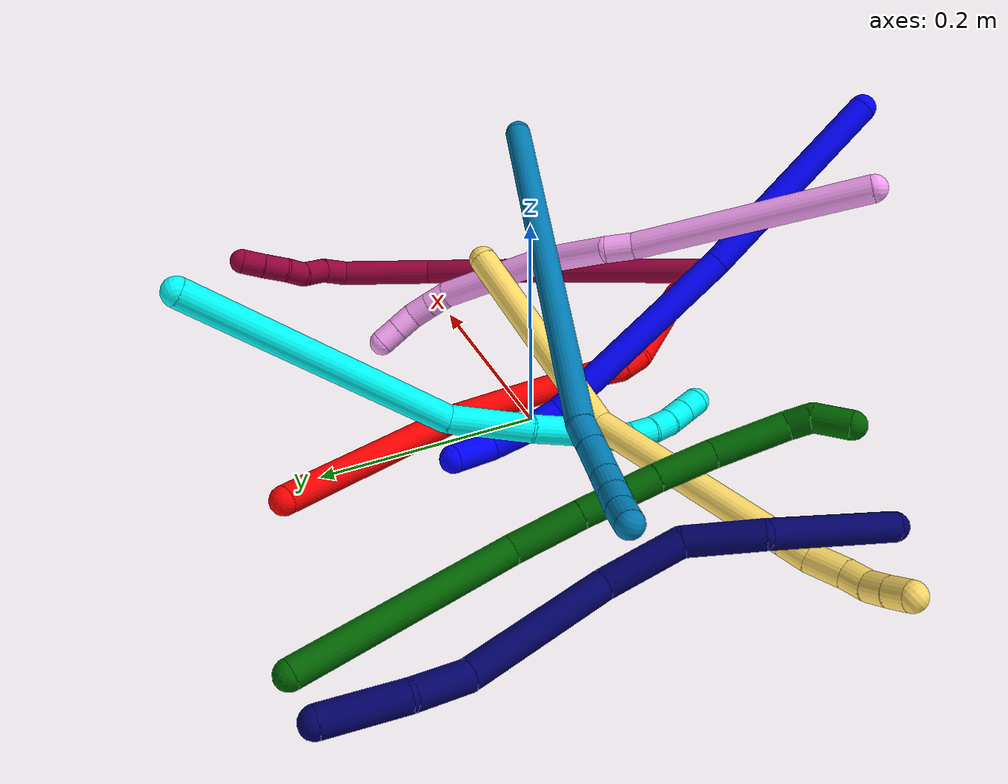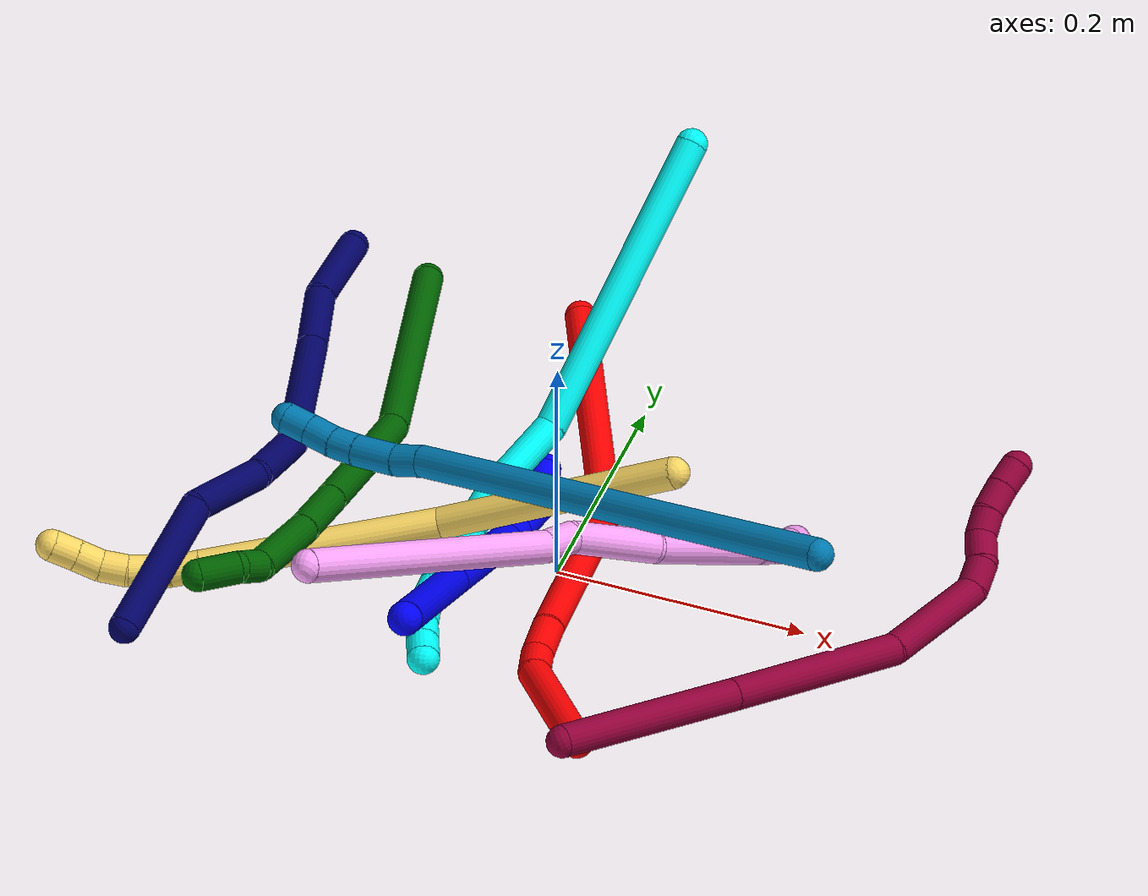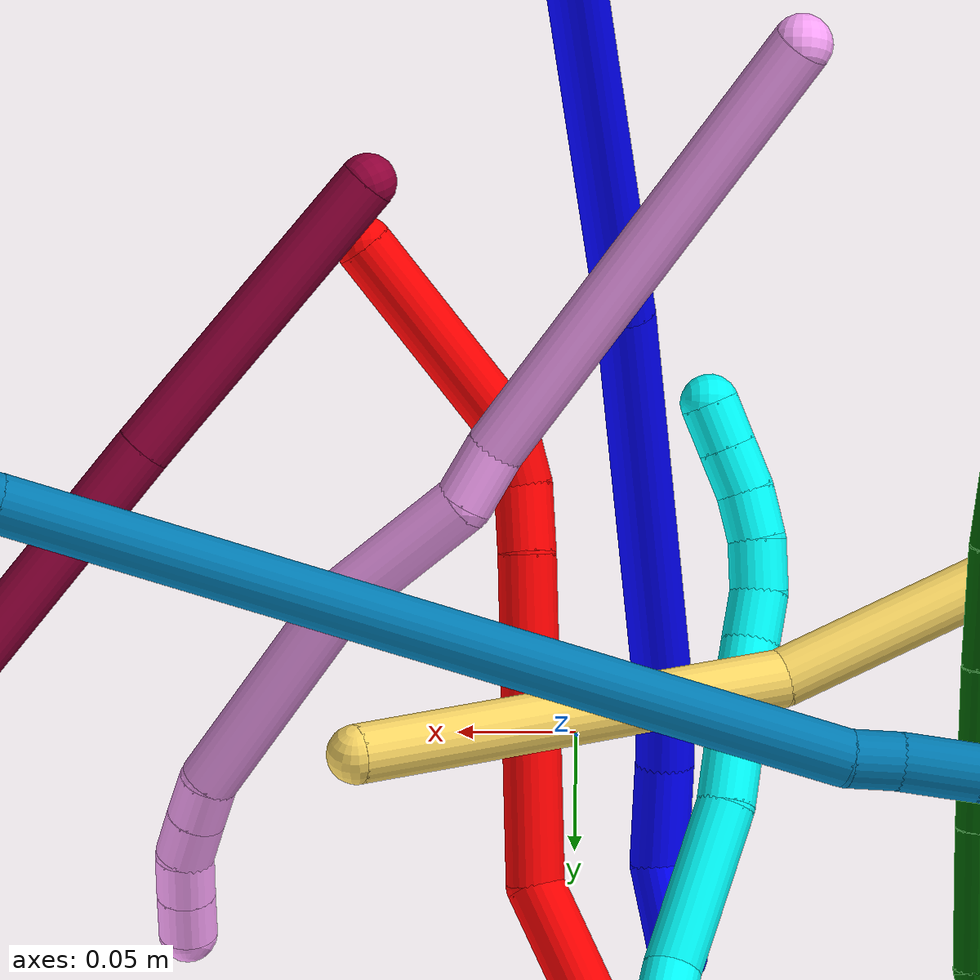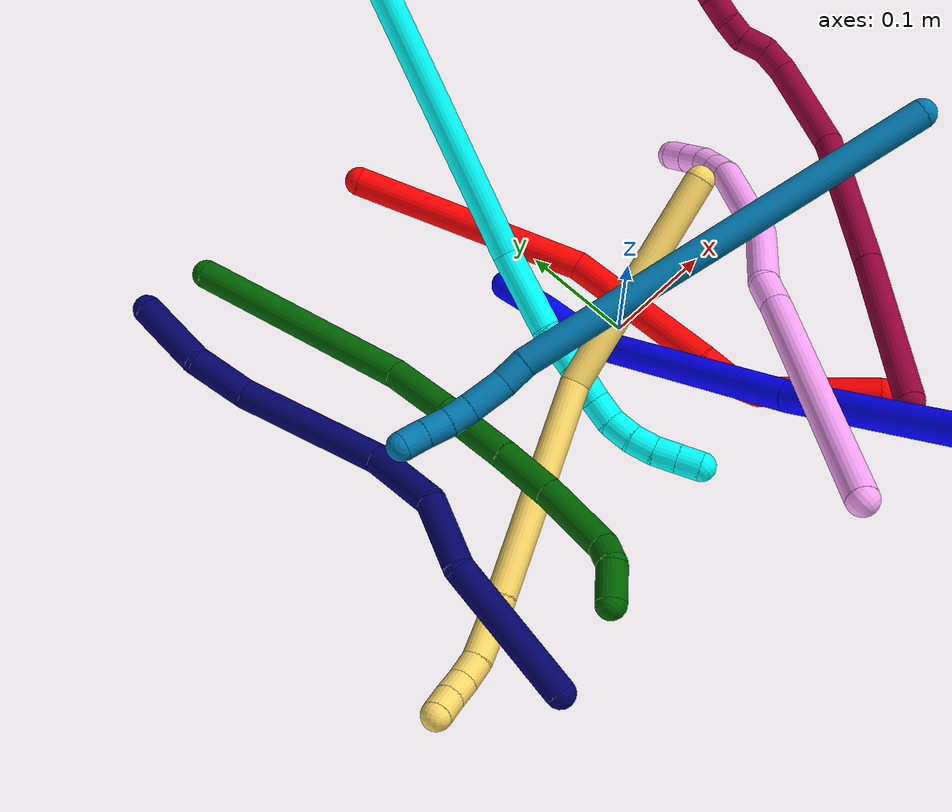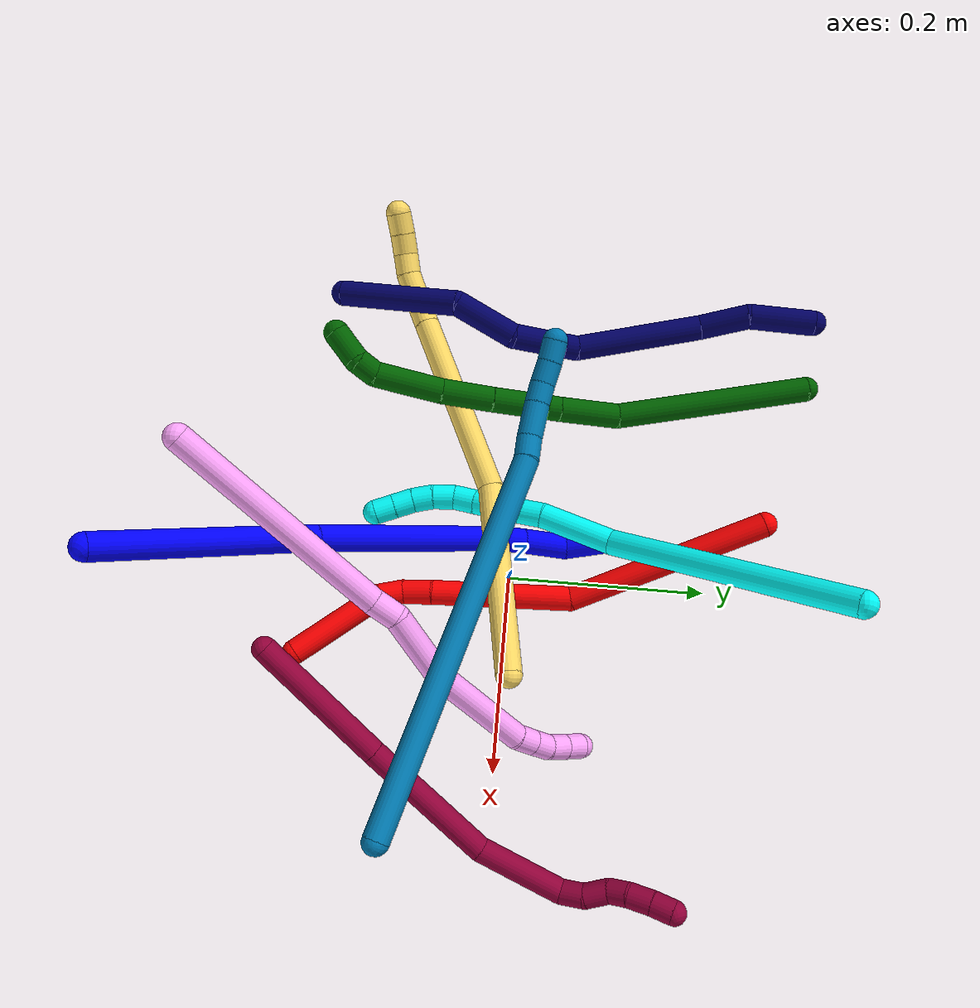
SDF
<sdf version="1.7">
 <world name="default">
  <plugin name="TubeGeneratorPlugin" filename="libtube_generator_plugin.so"/>
  <model name="photoneo_s_sensor">
   <static>1</static>
   <pose>0 0 2 1.57079 1.57079 3.14159</pose>
   <link name="link">
    <inertial><mass>0.1</mass></inertial>
    <sensor name="sensor" type="depth">
     <update_rate>30</update_rate>
     <camera>
      <horizontal_fov>1.22</horizontal_fov>
      <image><width>1920</width><height>1200</height><format>B8G8R8</format></image>
      <clip><near>0.1</near><far>4</far></clip>
      <depth_camera><output>points</output></depth_camera>
     </camera>
     <plugin name="camera_plugin" filename="libgazebo_ros_depth_camera.so">
      <baseline>0.2</baseline>
      <alwaysOn>1</alwaysOn>
      <updateRate>0.0</updateRate>
      <cameraName>camera_ir</cameraName>
      <imageTopicName>/camera/color/image_raw</imageTopicName>
      <cameraInfoTopicName>/camera/color/camera_info</cameraInfoTopicName>
      <depthImageTopicName>/camera/depth/image_raw</depthImageTopicName>
      <depthImageCameraInfoTopicName>/camera/depth/camera_info</depthImageCameraInfoTopicName>
      <pointCloudTopicName>/camera/depth/points</pointCloudTopicName>
      <frameName>fr_optical</frameName>
      <pointCloudCutoff>0.1</pointCloudCutoff>
      <pointCloudCutoffMax>2.0</pointCloudCutoffMax>
      <distortionK1>0</distortionK1>
      <distortionK2>0</distortionK2>
      <distortionK3>0</distortionK3>
      <distortionT1>0</distortionT1>
      <distortionT2>0</distortionT2>
      <CxPrime>0</CxPrime>
      <Cx>0</Cx>
      <Cy>0</Cy>
      <focalLength>0</focalLength>
      <hackBaseline>0</hackBaseline>
     </plugin>
    </sensor>
   </link>
  </model>
  <gravity>0 0 -9.8</gravity>
  <magnetic_field>6e-06 2.3e-05 -4.2e-05</magnetic_field>
  <atmosphere type="adiabatic"/>
  <physics name="default_physics" default="0" type="ode">
   <max_step_size>0.003</max_step_size>
   <real_time_factor>1</real_time_factor>
   <real_time_update_rate>1000</real_time_update_rate>
   <max_contacts>10000</max_contacts>
   <ode>
    <solver>
     <type>quick</type>
     <iters>100</iters>
     <sor>1.3</sor>
     <use_dynamic_moi_rescaling>0</use_dynamic_moi_rescaling>
    </solver>
    <constraints>
     <contact_max_correcting_vel>0</contact_max_correcting_vel>
     <contact_surface_layer>0.001</contact_surface_layer>
     <cfm>0</cfm>
     <erp>0.2</erp>
    </constraints>
   </ode>
  </physics>
  <scene><ambient>0.4 0.4 0.4 1</ambient><background>0.7 0.7 0.7 1</background><shadows>0</shadows></scene>
  <audio><device>default</device></audio>
  <spherical_coordinates>
   <surface_model>EARTH_WGS84</surface_model>
   <latitude_deg>0</latitude_deg>
   <longitude_deg>0</longitude_deg>
   <elevation>0</elevation>
   <heading_deg>0</heading_deg>
  </spherical_coordinates>
  <model name="bin">
   <static>1</static>
   <link name="bottom">
    <collision name="collision-bottom">
     <pose>0 0 -0.01 0 -0 0</pose>
     <geometry><box><size>0.8 0.6 0.02</size></box></geometry>
     <surface>
      <friction><ode><mu>100</mu><mu2>100</mu2></ode></friction>
      <contact><collide_bitmask>65535</collide_bitmask></contact>
     </surface>
    </collision>
   </link>
   <link name="west_wall">
    <collision name="collision-west_wall">
     <pose>-0.41 0 0.1 0 -0 0</pose>
     <geometry><box><size>0.02 0.6 0.2</size></box></geometry>
     <surface>
      <friction><ode><mu>100</mu><mu2>100</mu2></ode></friction>
      <contact><collide_bitmask>65535</collide_bitmask></contact>
     </surface>
    </collision>
   </link>
   <link name="east_wall">
    <collision name="collision-east_wall">
     <pose>0.41 0 0.1 0 -0 0</pose>
     <geometry><box><size>0.02 0.6 0.2</size></box></geometry>
     <surface>
      <friction><ode><mu>100</mu><mu2>100</mu2></ode></friction>
      <contact><collide_bitmask>65535</collide_bitmask></contact>
     </surface>
    </collision>
   </link>
   <link name="south_wall">
    <collision name="collision-south_wall">
     <pose>0 -0.31 0.1 0 -0 0</pose>
     <geometry><box><size>0.8 0.02 0.2</size></box></geometry>
     <surface>
      <friction><ode><mu>100</mu><mu2>100</mu2></ode></friction>
      <contact><collide_bitmask>65535</collide_bitmask></contact>
     </surface>
    </collision>
   </link>
   <link name="north_wall">
    <collision name="collision-north_wall">
     <pose>0 0.31 0.1 0 -0 0</pose>
     <geometry><box><size>0.8 0.02 0.2</size></box></geometry>
     <surface>
      <friction><ode><mu>100</mu><mu2>100</mu2></ode></friction>
      <contact><collide_bitmask>65535</collide_bitmask></contact>
     </surface>
    </collision>
   </link>
  </model>
  <model name="1">
   <static>0</static>
   <link name="1">
    <collision name="collision-cylinder-e_1_1_4">
     <pose>0.007891 0.068695 -0.070158 -2.36673 0.080194 -0.196003</pose>
     <geometry><cylinder><radius>0.0125</radius><length>0.197012</length></cylinder></geometry>
     <surface>
      <friction><ode><mu>1.16</mu><mu2>1.16</mu2><slip1>0</slip1><slip2>0</slip2></ode></friction>
      <contact><ode><kp>1e+06</kp><kd>1</kd><max_vel>0</max_vel><min_depth>0.001</min_depth></ode></contact>
     </surface>
    </collision>
    <visual name="visual-cylinder-e_1_1_4">
     <pose>0.007891 0.068695 -0.070158 -2.36673 0.080194 -0.196003</pose>
     <geometry><cylinder><radius>0.0125</radius><length>0.197012</length></cylinder></geometry>
     <material><ambient>0 0 1 1</ambient></material>
    </visual>
    <collision name="collision-cylinder-e_2_4_5">
     <pose>0.022717 0.209499 -0.205709 -2.3074 0.071117 -0.160224</pose>
     <geometry><cylinder><radius>0.0125</radius><length>0.195182</length></cylinder></geometry>
     <surface>
      <friction><ode><mu>1.16</mu><mu2>1.16</mu2><slip1>0</slip1><slip2>0</slip2></ode></friction>
      <contact><ode><kp>1e+06</kp><kd>1</kd><max_vel>0</max_vel><min_depth>0.001</min_depth></ode></contact>
     </surface>
    </collision>
    <visual name="visual-cylinder-e_2_4_5">
     <pose>0.022717 0.209499 -0.205709 -2.3074 0.071117 -0.160224</pose>
     <geometry><cylinder><radius>0.0125</radius><length>0.195182</length></cylinder></geometry>
     <material><ambient>0 0 1 1</ambient></material>
    </visual>
    <collision name="collision-cylinder-e_3_5_6">
     <pose>0.029596 0.291521 -0.277165 -2.11966 -0.004747 0.008467</pose>
     <geometry><cylinder><radius>0.0125</radius><length>0.023241</length></cylinder></geometry>
     <surface>
      <friction><ode><mu>1.16</mu><mu2>1.16</mu2><slip1>0</slip1><slip2>0</slip2></ode></friction>
      <contact><ode><kp>1e+06</kp><kd>1</kd><max_vel>0</max_vel><min_depth>0.001</min_depth></ode></contact>
     </surface>
    </collision>
    <visual name="visual-cylinder-e_3_5_6">
     <pose>0.029596 0.291521 -0.277165 -2.11966 -0.004747 0.008467</pose>
     <geometry><cylinder><radius>0.0125</radius><length>0.023241</length></cylinder></geometry>
     <material><ambient>0 0 1 1</ambient></material>
    </visual>
    <collision name="collision-cylinder-e_4_6_7">
     <pose>0.02797 0.3215 -0.292742 -2.01355 -0.070645 0.11161</pose>
     <geometry><cylinder><radius>0.0125</radius><length>0.044524</length></cylinder></geometry>
     <surface>
      <friction><ode><mu>1.16</mu><mu2>1.16</mu2><slip1>0</slip1><slip2>0</slip2></ode></friction>
      <contact><ode><kp>1e+06</kp><kd>1</kd><max_vel>0</max_vel><min_depth>0.001</min_depth></ode></contact>
     </surface>
    </collision>
    <visual name="visual-cylinder-e_4_6_7">
     <pose>0.02797 0.3215 -0.292742 -2.01355 -0.070645 0.11161</pose>
     <geometry><cylinder><radius>0.0125</radius><length>0.044524</length></cylinder></geometry>
     <material><ambient>0 0 1 1</ambient></material>
    </visual>
    <collision name="collision-cylinder-e_5_7_2">
     <pose>0.016504 0.357515 -0.309222 -1.9826 -0.516934 0.767853</pose>
     <geometry><cylinder><radius>0.0125</radius><length>0.04004</length></cylinder></geometry>
     <surface>
      <friction><ode><mu>1.16</mu><mu2>1.16</mu2><slip1>0</slip1><slip2>0</slip2></ode></friction>
      <contact><ode><kp>1e+06</kp><kd>1</kd><max_vel>0</max_vel><min_depth>0.001</min_depth></ode></contact>
     </surface>
    </collision>
    <visual name="visual-cylinder-e_5_7_2">
     <pose>0.016504 0.357515 -0.309222 -1.9826 -0.516934 0.767853</pose>
     <geometry><cylinder><radius>0.0125</radius><length>0.04004</length></cylinder></geometry>
     <material><ambient>0 0 1 1</ambient></material>
    </visual>
    <collision name="collision-sphere-2">
     <pose>0.00661 0.373464 -0.316188 0 -0 0</pose>
     <geometry><sphere><radius>0.0125</radius></sphere></geometry>
     <surface>
      <friction><ode><mu>1.16</mu><mu2>1.16</mu2><slip1>0</slip1><slip2>0</slip2></ode></friction>
      <contact><ode><kp>1e+06</kp><kd>1</kd><max_vel>0</max_vel><min_depth>0.001</min_depth></ode></contact>
     </surface>
    </collision>
    <visual name="visual-sphere-2">
     <pose>0.00661 0.373464 -0.316188 0 -0 0</pose>
     <geometry><sphere><radius>0.0125</radius></sphere></geometry>
     <material><ambient>0 0 1 1</ambient></material>
    </visual>
    <collision name="collision-sphere-7">
     <pose>0.026398 0.341565 -0.302256 0 -0 0</pose>
     <geometry><sphere><radius>0.0125</radius></sphere></geometry>
     <surface>
      <friction><ode><mu>1.16</mu><mu2>1.16</mu2><slip1>0</slip1><slip2>0</slip2></ode></friction>
      <contact><ode><kp>1e+06</kp><kd>1</kd><max_vel>0</max_vel><min_depth>0.001</min_depth></ode></contact>
     </surface>
    </collision>
    <visual name="visual-sphere-7">
     <pose>0.026398 0.341565 -0.302256 0 -0 0</pose>
     <geometry><sphere><radius>0.0125</radius></sphere></geometry>
     <material><ambient>0 0 1 1</ambient></material>
    </visual>
    <collision name="collision-sphere-6">
     <pose>0.029541 0.301435 -0.283228 0 -0 0</pose>
     <geometry><sphere><radius>0.0125</radius></sphere></geometry>
     <surface>
      <friction><ode><mu>1.16</mu><mu2>1.16</mu2><slip1>0</slip1><slip2>0</slip2></ode></friction>
      <contact><ode><kp>1e+06</kp><kd>1</kd><max_vel>0</max_vel><min_depth>0.001</min_depth></ode></contact>
     </surface>
    </collision>
    <visual name="visual-sphere-6">
     <pose>0.029541 0.301435 -0.283228 0 -0 0</pose>
     <geometry><sphere><radius>0.0125</radius></sphere></geometry>
     <material><ambient>0 0 1 1</ambient></material>
    </visual>
    <collision name="collision-sphere-5">
     <pose>0.029651 0.281607 -0.271102 0 -0 0</pose>
     <geometry><sphere><radius>0.0125</radius></sphere></geometry>
     <surface>
      <friction><ode><mu>1.16</mu><mu2>1.16</mu2><slip1>0</slip1><slip2>0</slip2></ode></friction>
      <contact><ode><kp>1e+06</kp><kd>1</kd><max_vel>0</max_vel><min_depth>0.001</min_depth></ode></contact>
     </surface>
    </collision>
    <visual name="visual-sphere-5">
     <pose>0.029651 0.281607 -0.271102 0 -0 0</pose>
     <geometry><sphere><radius>0.0125</radius></sphere></geometry>
     <material><ambient>0 0 1 1</ambient></material>
    </visual>
    <collision name="collision-sphere-1">
     <geometry><sphere><radius>0.0125</radius></sphere></geometry>
     <surface>
      <friction><ode><mu>1.16</mu><mu2>1.16</mu2><slip1>0</slip1><slip2>0</slip2></ode></friction>
      <contact><ode><kp>1e+06</kp><kd>1</kd><max_vel>0</max_vel><min_depth>0.001</min_depth></ode></contact>
     </surface>
    </collision>
    <visual name="visual-sphere-1">
     <geometry><sphere><radius>0.0125</radius></sphere></geometry>
     <material><ambient>0 0 1 1</ambient></material>
    </visual>
    <collision name="collision-sphere-4">
     <pose>0.015782 0.137391 -0.140316 0 -0 0</pose>
     <geometry><sphere><radius>0.0125</radius></sphere></geometry>
     <surface>
      <friction><ode><mu>1.16</mu><mu2>1.16</mu2><slip1>0</slip1><slip2>0</slip2></ode></friction>
      <contact><ode><kp>1e+06</kp><kd>1</kd><max_vel>0</max_vel><min_depth>0.001</min_depth></ode></contact>
     </surface>
    </collision>
    <visual name="visual-sphere-4">
     <pose>0.015782 0.137391 -0.140316 0 -0 0</pose>
     <geometry><sphere><radius>0.0125</radius></sphere></geometry>
     <material><ambient>0 0 1 1</ambient></material>
    </visual>
    <inertial>
     <pose>0.017165 0.179658 -0.17166 0 -0 0</pose>
     <mass>0.5</mass>
     <inertia>
      <ixx>0.001044</ixx>
      <ixy>0</ixy>
      <ixz>0</ixz>
      <iyy>-0.001051</iyy>
      <iyz>0</iyz>
      <izz>-0.001045</izz>
     </inertia>
    </inertial>
   </link>
   <pose>0.011148 -0.338486 0.239513 -0.01331 0.822768 -0.431208</pose>
  </model>
  <model name="2">
   <static>0</static>
   <link name="2">
    <collision name="collision-cylinder-e_1_1_4">
     <pose>0.03027 -0.095128 0.023469 1.32892 0.299633 0.235375</pose>
     <geometry><cylinder><radius>0.0125</radius><length>0.205099</length></cylinder></geometry>
     <surface>
      <friction><ode><mu>1.16</mu><mu2>1.16</mu2><slip1>0</slip1><slip2>0</slip2></ode></friction>
      <contact><ode><kp>1e+06</kp><kd>1</kd><max_vel>0</max_vel><min_depth>0.001</min_depth></ode></contact>
     </surface>
    </collision>
    <visual name="visual-cylinder-e_1_1_4">
     <pose>0.03027 -0.095128 0.023469 1.32892 0.299633 0.235375</pose>
     <geometry><cylinder><radius>0.0125</radius><length>0.205099</length></cylinder></geometry>
     <material><ambient>1 0 0 1</ambient></material>
    </visual>
    <collision name="collision-cylinder-e_2_4_5">
     <pose>0.078178 -0.256707 0.03181 1.79462 0.253266 0.31644</pose>
     <geometry><cylinder><radius>0.0125</radius><length>0.140792</length></cylinder></geometry>
     <surface>
      <friction><ode><mu>1.16</mu><mu2>1.16</mu2><slip1>0</slip1><slip2>0</slip2></ode></friction>
      <contact><ode><kp>1e+06</kp><kd>1</kd><max_vel>0</max_vel><min_depth>0.001</min_depth></ode></contact>
     </surface>
    </collision>
    <visual name="visual-cylinder-e_2_4_5">
     <pose>0.078178 -0.256707 0.03181 1.79462 0.253266 0.31644</pose>
     <geometry><cylinder><radius>0.0125</radius><length>0.140792</length></cylinder></geometry>
     <material><ambient>1 0 0 1</ambient></material>
    </visual>
    <collision name="collision-cylinder-e_3_5_6">
     <pose>0.101157 -0.336719 0.014519 1.72908 0.370855 0.432908</pose>
     <geometry><cylinder><radius>0.0125</radius><length>0.029471</length></cylinder></geometry>
     <surface>
      <friction><ode><mu>1.16</mu><mu2>1.16</mu2><slip1>0</slip1><slip2>0</slip2></ode></friction>
      <contact><ode><kp>1e+06</kp><kd>1</kd><max_vel>0</max_vel><min_depth>0.001</min_depth></ode></contact>
     </surface>
    </collision>
    <visual name="visual-cylinder-e_3_5_6">
     <pose>0.101157 -0.336719 0.014519 1.72908 0.370855 0.432908</pose>
     <geometry><cylinder><radius>0.0125</radius><length>0.029471</length></cylinder></geometry>
     <material><ambient>1 0 0 1</ambient></material>
    </visual>
    <collision name="collision-cylinder-e_4_6_7">
     <pose>0.107379 -0.362482 0.011912 1.60698 0.072069 0.074722</pose>
     <geometry><cylinder><radius>0.0125</radius><length>0.02448</length></cylinder></geometry>
     <surface>
      <friction><ode><mu>1.16</mu><mu2>1.16</mu2><slip1>0</slip1><slip2>0</slip2></ode></friction>
      <contact><ode><kp>1e+06</kp><kd>1</kd><max_vel>0</max_vel><min_depth>0.001</min_depth></ode></contact>
     </surface>
    </collision>
    <visual name="visual-cylinder-e_4_6_7">
     <pose>0.107379 -0.362482 0.011912 1.60698 0.072069 0.074722</pose>
     <geometry><cylinder><radius>0.0125</radius><length>0.02448</length></cylinder></geometry>
     <material><ambient>1 0 0 1</ambient></material>
    </visual>
    <collision name="collision-cylinder-e_5_7_2">
     <pose>0.103815 -0.421677 0.028192 1.22894 -0.088891 -0.062742</pose>
     <geometry><cylinder><radius>0.0125</radius><length>0.100157</length></cylinder></geometry>
     <surface>
      <friction><ode><mu>1.16</mu><mu2>1.16</mu2><slip1>0</slip1><slip2>0</slip2></ode></friction>
      <contact><ode><kp>1e+06</kp><kd>1</kd><max_vel>0</max_vel><min_depth>0.001</min_depth></ode></contact>
     </surface>
    </collision>
    <visual name="visual-cylinder-e_5_7_2">
     <pose>0.103815 -0.421677 0.028192 1.22894 -0.088891 -0.062742</pose>
     <geometry><cylinder><radius>0.0125</radius><length>0.100157</length></cylinder></geometry>
     <material><ambient>1 0 0 1</ambient></material>
    </visual>
    <collision name="collision-sphere-2">
     <pose>0.099369 -0.468672 0.044914 0 -0 0</pose>
     <geometry><sphere><radius>0.0125</radius></sphere></geometry>
     <surface>
      <friction><ode><mu>1.16</mu><mu2>1.16</mu2><slip1>0</slip1><slip2>0</slip2></ode></friction>
      <contact><ode><kp>1e+06</kp><kd>1</kd><max_vel>0</max_vel><min_depth>0.001</min_depth></ode></contact>
     </surface>
    </collision>
    <visual name="visual-sphere-2">
     <pose>0.099369 -0.468672 0.044914 0 -0 0</pose>
     <geometry><sphere><radius>0.0125</radius></sphere></geometry>
     <material><ambient>1 0 0 1</ambient></material>
    </visual>
    <collision name="collision-sphere-7">
     <pose>0.10826 -0.374682 0.011471 0 -0 0</pose>
     <geometry><sphere><radius>0.0125</radius></sphere></geometry>
     <surface>
      <friction><ode><mu>1.16</mu><mu2>1.16</mu2><slip1>0</slip1><slip2>0</slip2></ode></friction>
      <contact><ode><kp>1e+06</kp><kd>1</kd><max_vel>0</max_vel><min_depth>0.001</min_depth></ode></contact>
     </surface>
    </collision>
    <visual name="visual-sphere-7">
     <pose>0.10826 -0.374682 0.011471 0 -0 0</pose>
     <geometry><sphere><radius>0.0125</radius></sphere></geometry>
     <material><ambient>1 0 0 1</ambient></material>
    </visual>
    <collision name="collision-sphere-6">
     <pose>0.106498 -0.350281 0.012354 0 -0 0</pose>
     <geometry><sphere><radius>0.0125</radius></sphere></geometry>
     <surface>
      <friction><ode><mu>1.16</mu><mu2>1.16</mu2><slip1>0</slip1><slip2>0</slip2></ode></friction>
      <contact><ode><kp>1e+06</kp><kd>1</kd><max_vel>0</max_vel><min_depth>0.001</min_depth></ode></contact>
     </surface>
    </collision>
    <visual name="visual-sphere-6">
     <pose>0.106498 -0.350281 0.012354 0 -0 0</pose>
     <geometry><sphere><radius>0.0125</radius></sphere></geometry>
     <material><ambient>1 0 0 1</ambient></material>
    </visual>
    <collision name="collision-sphere-5">
     <pose>0.095817 -0.323158 0.016683 0 -0 0</pose>
     <geometry><sphere><radius>0.0125</radius></sphere></geometry>
     <surface>
      <friction><ode><mu>1.16</mu><mu2>1.16</mu2><slip1>0</slip1><slip2>0</slip2></ode></friction>
      <contact><ode><kp>1e+06</kp><kd>1</kd><max_vel>0</max_vel><min_depth>0.001</min_depth></ode></contact>
     </surface>
    </collision>
    <visual name="visual-sphere-5">
     <pose>0.095817 -0.323158 0.016683 0 -0 0</pose>
     <geometry><sphere><radius>0.0125</radius></sphere></geometry>
     <material><ambient>1 0 0 1</ambient></material>
    </visual>
    <collision name="collision-sphere-1">
     <geometry><sphere><radius>0.0125</radius></sphere></geometry>
     <surface>
      <friction><ode><mu>1.16</mu><mu2>1.16</mu2><slip1>0</slip1><slip2>0</slip2></ode></friction>
      <contact><ode><kp>1e+06</kp><kd>1</kd><max_vel>0</max_vel><min_depth>0.001</min_depth></ode></contact>
     </surface>
    </collision>
    <visual name="visual-sphere-1">
     <geometry><sphere><radius>0.0125</radius></sphere></geometry>
     <material><ambient>1 0 0 1</ambient></material>
    </visual>
    <collision name="collision-sphere-4">
     <pose>0.060539 -0.190257 0.046937 0 -0 0</pose>
     <geometry><sphere><radius>0.0125</radius></sphere></geometry>
     <surface>
      <friction><ode><mu>1.16</mu><mu2>1.16</mu2><slip1>0</slip1><slip2>0</slip2></ode></friction>
      <contact><ode><kp>1e+06</kp><kd>1</kd><max_vel>0</max_vel><min_depth>0.001</min_depth></ode></contact>
     </surface>
    </collision>
    <visual name="visual-sphere-4">
     <pose>0.060539 -0.190257 0.046937 0 -0 0</pose>
     <geometry><sphere><radius>0.0125</radius></sphere></geometry>
     <material><ambient>1 0 0 1</ambient></material>
    </visual>
    <inertial>
     <pose>0.066446 -0.233369 0.02567 0 -0 0</pose>
     <mass>0.5</mass>
     <inertia>
      <ixx>0.001224</ixx>
      <ixy>0</ixy>
      <ixz>0</ixz>
      <iyy>0.000409</iyy>
      <iyz>0</iyz>
      <izz>0.000722</izz>
     </inertia>
    </inertial>
   </link>
   <pose>-0.071509 0.246716 0.045144 -2.56804 1.19625 -2.27744</pose>
  </model>
  <model name="3">
   <static>0</static>
   <link name="3">
    <collision name="collision-cylinder-e_1_1_4">
     <pose>-0.072334 -0.095496 -0.032103 1.8951 -0.622682 -0.841857</pose>
     <geometry><cylinder><radius>0.0125</radius><length>0.248051</length></cylinder></geometry>
     <surface>
      <friction><ode><mu>1.16</mu><mu2>1.16</mu2><slip1>0</slip1><slip2>0</slip2></ode></friction>
      <contact><ode><kp>1e+06</kp><kd>1</kd><max_vel>0</max_vel><min_depth>0.001</min_depth></ode></contact>
     </surface>
    </collision>
    <visual name="visual-cylinder-e_1_1_4">
     <pose>-0.072334 -0.095496 -0.032103 1.8951 -0.622682 -0.841857</pose>
     <geometry><cylinder><radius>0.0125</radius><length>0.248051</length></cylinder></geometry>
     <material><ambient>0.003922 1 0.996078 1</ambient></material>
    </visual>
    <collision name="collision-cylinder-e_2_4_5">
     <pose>-0.175981 -0.207664 -0.073861 2.0957 -1.01925 -1.53977</pose>
     <geometry><cylinder><radius>0.0125</radius><length>0.07353</length></cylinder></geometry>
     <surface>
      <friction><ode><mu>1.16</mu><mu2>1.16</mu2><slip1>0</slip1><slip2>0</slip2></ode></friction>
      <contact><ode><kp>1e+06</kp><kd>1</kd><max_vel>0</max_vel><min_depth>0.001</min_depth></ode></contact>
     </surface>
    </collision>
    <visual name="visual-cylinder-e_2_4_5">
     <pose>-0.175981 -0.207664 -0.073861 2.0957 -1.01925 -1.53977</pose>
     <geometry><cylinder><radius>0.0125</radius><length>0.07353</length></cylinder></geometry>
     <material><ambient>0.003922 1 0.996078 1</ambient></material>
    </visual>
    <collision name="collision-cylinder-e_3_5_6">
     <pose>-0.222618 -0.234475 -0.085532 1.76721 -0.977276 -1.14972</pose>
     <geometry><cylinder><radius>0.0125</radius><length>0.036971</length></cylinder></geometry>
     <surface>
      <friction><ode><mu>1.16</mu><mu2>1.16</mu2><slip1>0</slip1><slip2>0</slip2></ode></friction>
      <contact><ode><kp>1e+06</kp><kd>1</kd><max_vel>0</max_vel><min_depth>0.001</min_depth></ode></contact>
     </surface>
    </collision>
    <visual name="visual-cylinder-e_3_5_6">
     <pose>-0.222618 -0.234475 -0.085532 1.76721 -0.977276 -1.14972</pose>
     <geometry><cylinder><radius>0.0125</radius><length>0.036971</length></cylinder></geometry>
     <material><ambient>0.003922 1 0.996078 1</ambient></material>
    </visual>
    <collision name="collision-cylinder-e_4_6_7">
     <pose>-0.251656 -0.2553 -0.090341 1.82633 -0.892835 -1.10963</pose>
     <geometry><cylinder><radius>0.0125</radius><length>0.035215</length></cylinder></geometry>
     <surface>
      <friction><ode><mu>1.16</mu><mu2>1.16</mu2><slip1>0</slip1><slip2>0</slip2></ode></friction>
      <contact><ode><kp>1e+06</kp><kd>1</kd><max_vel>0</max_vel><min_depth>0.001</min_depth></ode></contact>
     </surface>
    </collision>
    <visual name="visual-cylinder-e_4_6_7">
     <pose>-0.251656 -0.2553 -0.090341 1.82633 -0.892835 -1.10963</pose>
     <geometry><cylinder><radius>0.0125</radius><length>0.035215</length></cylinder></geometry>
     <material><ambient>0.003922 1 0.996078 1</ambient></material>
    </visual>
    <collision name="collision-cylinder-e_5_7_8">
     <pose>-0.275244 -0.271332 -0.094433 1.80929 -1.06237 -1.28375</pose>
     <geometry><cylinder><radius>0.0125</radius><length>0.022609</length></cylinder></geometry>
     <surface>
      <friction><ode><mu>1.16</mu><mu2>1.16</mu2><slip1>0</slip1><slip2>0</slip2></ode></friction>
      <contact><ode><kp>1e+06</kp><kd>1</kd><max_vel>0</max_vel><min_depth>0.001</min_depth></ode></contact>
     </surface>
    </collision>
    <visual name="visual-cylinder-e_5_7_8">
     <pose>-0.275244 -0.271332 -0.094433 1.80929 -1.06237 -1.28375</pose>
     <geometry><cylinder><radius>0.0125</radius><length>0.022609</length></cylinder></geometry>
     <material><ambient>0.003922 1 0.996078 1</ambient></material>
    </visual>
    <collision name="collision-cylinder-e_6_8_9">
     <pose>-0.295317 -0.280917 -0.094266 1.23753 -1.15656 -0.870124</pose>
     <geometry><cylinder><radius>0.0125</radius><length>0.022282</length></cylinder></geometry>
     <surface>
      <friction><ode><mu>1.16</mu><mu2>1.16</mu2><slip1>0</slip1><slip2>0</slip2></ode></friction>
      <contact><ode><kp>1e+06</kp><kd>1</kd><max_vel>0</max_vel><min_depth>0.001</min_depth></ode></contact>
     </surface>
    </collision>
    <visual name="visual-cylinder-e_6_8_9">
     <pose>-0.295317 -0.280917 -0.094266 1.23753 -1.15656 -0.870124</pose>
     <geometry><cylinder><radius>0.0125</radius><length>0.022282</length></cylinder></geometry>
     <material><ambient>0.003922 1 0.996078 1</ambient></material>
    </visual>
    <collision name="collision-cylinder-e_7_9_10">
     <pose>-0.314443 -0.28956 -0.089479 0.924923 -1.01735 -0.542275</pose>
     <geometry><cylinder><radius>0.0125</radius><length>0.020989</length></cylinder></geometry>
     <surface>
      <friction><ode><mu>1.16</mu><mu2>1.16</mu2><slip1>0</slip1><slip2>0</slip2></ode></friction>
      <contact><ode><kp>1e+06</kp><kd>1</kd><max_vel>0</max_vel><min_depth>0.001</min_depth></ode></contact>
     </surface>
    </collision>
    <visual name="visual-cylinder-e_7_9_10">
     <pose>-0.314443 -0.28956 -0.089479 0.924923 -1.01735 -0.542275</pose>
     <geometry><cylinder><radius>0.0125</radius><length>0.020989</length></cylinder></geometry>
     <material><ambient>0.003922 1 0.996078 1</ambient></material>
    </visual>
    <collision name="collision-cylinder-e_8_10_11">
     <pose>-0.331567 -0.29759 -0.081401 0.651132 -0.940311 -0.339781</pose>
     <geometry><cylinder><radius>0.0125</radius><length>0.020293</length></cylinder></geometry>
     <surface>
      <friction><ode><mu>1.16</mu><mu2>1.16</mu2><slip1>0</slip1><slip2>0</slip2></ode></friction>
      <contact><ode><kp>1e+06</kp><kd>1</kd><max_vel>0</max_vel><min_depth>0.001</min_depth></ode></contact>
     </surface>
    </collision>
    <visual name="visual-cylinder-e_8_10_11">
     <pose>-0.331567 -0.29759 -0.081401 0.651132 -0.940311 -0.339781</pose>
     <geometry><cylinder><radius>0.0125</radius><length>0.020293</length></cylinder></geometry>
     <material><ambient>0.003922 1 0.996078 1</ambient></material>
    </visual>
    <collision name="collision-cylinder-e_9_11_2">
     <pose>-0.347874 -0.304821 -0.071971 0.657287 -0.941815 -0.343795</pose>
     <geometry><cylinder><radius>0.0125</radius><length>0.020061</length></cylinder></geometry>
     <surface>
      <friction><ode><mu>1.16</mu><mu2>1.16</mu2><slip1>0</slip1><slip2>0</slip2></ode></friction>
      <contact><ode><kp>1e+06</kp><kd>1</kd><max_vel>0</max_vel><min_depth>0.001</min_depth></ode></contact>
     </surface>
    </collision>
    <visual name="visual-cylinder-e_9_11_2">
     <pose>-0.347874 -0.304821 -0.071971 0.657287 -0.941815 -0.343795</pose>
     <geometry><cylinder><radius>0.0125</radius><length>0.020061</length></cylinder></geometry>
     <material><ambient>0.003922 1 0.996078 1</ambient></material>
    </visual>
    <collision name="collision-sphere-2">
     <pose>-0.355984 -0.308426 -0.0673 0 -0 0</pose>
     <geometry><sphere><radius>0.0125</radius></sphere></geometry>
     <surface>
      <friction><ode><mu>1.16</mu><mu2>1.16</mu2><slip1>0</slip1><slip2>0</slip2></ode></friction>
      <contact><ode><kp>1e+06</kp><kd>1</kd><max_vel>0</max_vel><min_depth>0.001</min_depth></ode></contact>
     </surface>
    </collision>
    <visual name="visual-sphere-2">
     <pose>-0.355984 -0.308426 -0.0673 0 -0 0</pose>
     <geometry><sphere><radius>0.0125</radius></sphere></geometry>
     <material><ambient>0.003922 1 0.996078 1</ambient></material>
    </visual>
    <collision name="collision-sphere-11">
     <pose>-0.339763 -0.301215 -0.076643 0 -0 0</pose>
     <geometry><sphere><radius>0.0125</radius></sphere></geometry>
     <surface>
      <friction><ode><mu>1.16</mu><mu2>1.16</mu2><slip1>0</slip1><slip2>0</slip2></ode></friction>
      <contact><ode><kp>1e+06</kp><kd>1</kd><max_vel>0</max_vel><min_depth>0.001</min_depth></ode></contact>
     </surface>
    </collision>
    <visual name="visual-sphere-11">
     <pose>-0.339763 -0.301215 -0.076643 0 -0 0</pose>
     <geometry><sphere><radius>0.0125</radius></sphere></geometry>
     <material><ambient>0.003922 1 0.996078 1</ambient></material>
    </visual>
    <collision name="collision-sphere-10">
     <pose>-0.323371 -0.293965 -0.086159 0 -0 0</pose>
     <geometry><sphere><radius>0.0125</radius></sphere></geometry>
     <surface>
      <friction><ode><mu>1.16</mu><mu2>1.16</mu2><slip1>0</slip1><slip2>0</slip2></ode></friction>
      <contact><ode><kp>1e+06</kp><kd>1</kd><max_vel>0</max_vel><min_depth>0.001</min_depth></ode></contact>
     </surface>
    </collision>
    <visual name="visual-sphere-10">
     <pose>-0.323371 -0.293965 -0.086159 0 -0 0</pose>
     <geometry><sphere><radius>0.0125</radius></sphere></geometry>
     <material><ambient>0.003922 1 0.996078 1</ambient></material>
    </visual>
    <collision name="collision-sphere-9">
     <pose>-0.305515 -0.285154 -0.092799 0 -0 0</pose>
     <geometry><sphere><radius>0.0125</radius></sphere></geometry>
     <surface>
      <friction><ode><mu>1.16</mu><mu2>1.16</mu2><slip1>0</slip1><slip2>0</slip2></ode></friction>
      <contact><ode><kp>1e+06</kp><kd>1</kd><max_vel>0</max_vel><min_depth>0.001</min_depth></ode></contact>
     </surface>
    </collision>
    <visual name="visual-sphere-9">
     <pose>-0.305515 -0.285154 -0.092799 0 -0 0</pose>
     <geometry><sphere><radius>0.0125</radius></sphere></geometry>
     <material><ambient>0.003922 1 0.996078 1</ambient></material>
    </visual>
    <collision name="collision-sphere-4">
     <pose>-0.144667 -0.190993 -0.064206 0 -0 0</pose>
     <geometry><sphere><radius>0.0125</radius></sphere></geometry>
     <surface>
      <friction><ode><mu>1.16</mu><mu2>1.16</mu2><slip1>0</slip1><slip2>0</slip2></ode></friction>
      <contact><ode><kp>1e+06</kp><kd>1</kd><max_vel>0</max_vel><min_depth>0.001</min_depth></ode></contact>
     </surface>
    </collision>
    <visual name="visual-sphere-4">
     <pose>-0.144667 -0.190993 -0.064206 0 -0 0</pose>
     <geometry><sphere><radius>0.0125</radius></sphere></geometry>
     <material><ambient>0.003922 1 0.996078 1</ambient></material>
    </visual>
    <collision name="collision-sphere-1">
     <geometry><sphere><radius>0.0125</radius></sphere></geometry>
     <surface>
      <friction><ode><mu>1.16</mu><mu2>1.16</mu2><slip1>0</slip1><slip2>0</slip2></ode></friction>
      <contact><ode><kp>1e+06</kp><kd>1</kd><max_vel>0</max_vel><min_depth>0.001</min_depth></ode></contact>
     </surface>
    </collision>
    <visual name="visual-sphere-1">
     <geometry><sphere><radius>0.0125</radius></sphere></geometry>
     <material><ambient>0.003922 1 0.996078 1</ambient></material>
    </visual>
    <collision name="collision-sphere-8">
     <pose>-0.285118 -0.27668 -0.095733 0 -0 0</pose>
     <geometry><sphere><radius>0.0125</radius></sphere></geometry>
     <surface>
      <friction><ode><mu>1.16</mu><mu2>1.16</mu2><slip1>0</slip1><slip2>0</slip2></ode></friction>
      <contact><ode><kp>1e+06</kp><kd>1</kd><max_vel>0</max_vel><min_depth>0.001</min_depth></ode></contact>
     </surface>
    </collision>
    <visual name="visual-sphere-8">
     <pose>-0.285118 -0.27668 -0.095733 0 -0 0</pose>
     <geometry><sphere><radius>0.0125</radius></sphere></geometry>
     <material><ambient>0.003922 1 0.996078 1</ambient></material>
    </visual>
    <collision name="collision-sphere-5">
     <pose>-0.207294 -0.224335 -0.083515 0 -0 0</pose>
     <geometry><sphere><radius>0.0125</radius></sphere></geometry>
     <surface>
      <friction><ode><mu>1.16</mu><mu2>1.16</mu2><slip1>0</slip1><slip2>0</slip2></ode></friction>
      <contact><ode><kp>1e+06</kp><kd>1</kd><max_vel>0</max_vel><min_depth>0.001</min_depth></ode></contact>
     </surface>
    </collision>
    <visual name="visual-sphere-5">
     <pose>-0.207294 -0.224335 -0.083515 0 -0 0</pose>
     <geometry><sphere><radius>0.0125</radius></sphere></geometry>
     <material><ambient>0.003922 1 0.996078 1</ambient></material>
    </visual>
    <collision name="collision-sphere-6">
     <pose>-0.237942 -0.244615 -0.08755 0 -0 0</pose>
     <geometry><sphere><radius>0.0125</radius></sphere></geometry>
     <surface>
      <friction><ode><mu>1.16</mu><mu2>1.16</mu2><slip1>0</slip1><slip2>0</slip2></ode></friction>
      <contact><ode><kp>1e+06</kp><kd>1</kd><max_vel>0</max_vel><min_depth>0.001</min_depth></ode></contact>
     </surface>
    </collision>
    <visual name="visual-sphere-6">
     <pose>-0.237942 -0.244615 -0.08755 0 -0 0</pose>
     <geometry><sphere><radius>0.0125</radius></sphere></geometry>
     <material><ambient>0.003922 1 0.996078 1</ambient></material>
    </visual>
    <collision name="collision-sphere-7">
     <pose>-0.265369 -0.265985 -0.093133 0 -0 0</pose>
     <geometry><sphere><radius>0.0125</radius></sphere></geometry>
     <surface>
      <friction><ode><mu>1.16</mu><mu2>1.16</mu2><slip1>0</slip1><slip2>0</slip2></ode></friction>
      <contact><ode><kp>1e+06</kp><kd>1</kd><max_vel>0</max_vel><min_depth>0.001</min_depth></ode></contact>
     </surface>
    </collision>
    <visual name="visual-sphere-7">
     <pose>-0.265369 -0.265985 -0.093133 0 -0 0</pose>
     <geometry><sphere><radius>0.0125</radius></sphere></geometry>
     <material><ambient>0.003922 1 0.996078 1</ambient></material>
    </visual>
    <inertial>
     <pose>-0.162169 -0.174484 -0.057894 0 -0 0</pose>
     <mass>0.5</mass>
     <inertia>
      <ixx>-0.000132</ixx>
      <ixy>0</ixy>
      <ixz>0</ixz>
      <iyy>-0.000532</iyy>
      <iyz>0</iyz>
      <izz>0.001801</izz>
     </inertia>
    </inertial>
   </link>
   <pose>0.003988 0.2902 0.206008 1.28815 0.306606 1.38576</pose>
  </model>
  <model name="4">
   <static>0</static>
   <link name="4">
    <collision name="collision-cylinder-e_1_1_4">
     <pose>0.030384 0.073191 -0.074154 -2.36273 0.283754 -0.669872</pose>
     <geometry><cylinder><radius>0.0125</radius><length>0.217062</length></cylinder></geometry>
     <surface>
      <friction><ode><mu>1.16</mu><mu2>1.16</mu2><slip1>0</slip1><slip2>0</slip2></ode></friction>
      <contact><ode><kp>1e+06</kp><kd>1</kd><max_vel>0</max_vel><min_depth>0.001</min_depth></ode></contact>
     </surface>
    </collision>
    <visual name="visual-cylinder-e_1_1_4">
     <pose>0.030384 0.073191 -0.074154 -2.36273 0.283754 -0.669872</pose>
     <geometry><cylinder><radius>0.0125</radius><length>0.217062</length></cylinder></geometry>
     <material><ambient>1 0.65098 0.996078 1</ambient></material>
    </visual>
    <collision name="collision-cylinder-e_2_4_5">
     <pose>0.063017 0.153676 -0.158927 -2.53976 0.172778 -0.544283</pose>
     <geometry><cylinder><radius>0.0125</radius><length>0.026154</length></cylinder></geometry>
     <surface>
      <friction><ode><mu>1.16</mu><mu2>1.16</mu2><slip1>0</slip1><slip2>0</slip2></ode></friction>
      <contact><ode><kp>1e+06</kp><kd>1</kd><max_vel>0</max_vel><min_depth>0.001</min_depth></ode></contact>
     </surface>
    </collision>
    <visual name="visual-cylinder-e_2_4_5">
     <pose>0.063017 0.153676 -0.158927 -2.53976 0.172778 -0.544283</pose>
     <geometry><cylinder><radius>0.0125</radius><length>0.026154</length></cylinder></geometry>
     <material><ambient>1 0.65098 0.996078 1</ambient></material>
    </visual>
    <collision name="collision-cylinder-e_3_5_6">
     <pose>0.073191 0.19035 -0.187761 -2.12577 0.225368 -0.401143</pose>
     <geometry><cylinder><radius>0.0125</radius><length>0.070932</length></cylinder></geometry>
     <surface>
      <friction><ode><mu>1.16</mu><mu2>1.16</mu2><slip1>0</slip1><slip2>0</slip2></ode></friction>
      <contact><ode><kp>1e+06</kp><kd>1</kd><max_vel>0</max_vel><min_depth>0.001</min_depth></ode></contact>
     </surface>
    </collision>
    <visual name="visual-cylinder-e_3_5_6">
     <pose>0.073191 0.19035 -0.187761 -2.12577 0.225368 -0.401143</pose>
     <geometry><cylinder><radius>0.0125</radius><length>0.070932</length></cylinder></geometry>
     <material><ambient>1 0.65098 0.996078 1</ambient></material>
    </visual>
    <collision name="collision-cylinder-e_4_6_7">
     <pose>0.100746 0.255095 -0.239765 -2.33343 0.381658 -0.848636</pose>
     <geometry><cylinder><radius>0.0125</radius><length>0.105407</length></cylinder></geometry>
     <surface>
      <friction><ode><mu>1.16</mu><mu2>1.16</mu2><slip1>0</slip1><slip2>0</slip2></ode></friction>
      <contact><ode><kp>1e+06</kp><kd>1</kd><max_vel>0</max_vel><min_depth>0.001</min_depth></ode></contact>
     </surface>
    </collision>
    <visual name="visual-cylinder-e_4_6_7">
     <pose>0.100746 0.255095 -0.239765 -2.33343 0.381658 -0.848636</pose>
     <geometry><cylinder><radius>0.0125</radius><length>0.105407</length></cylinder></geometry>
     <material><ambient>1 0.65098 0.996078 1</ambient></material>
    </visual>
    <collision name="collision-cylinder-e_5_7_8">
     <pose>0.125925 0.295183 -0.280532 -2.54644 0.582325 -1.54769</pose>
     <geometry><cylinder><radius>0.0125</radius><length>0.020178</length></cylinder></geometry>
     <surface>
      <friction><ode><mu>1.16</mu><mu2>1.16</mu2><slip1>0</slip1><slip2>0</slip2></ode></friction>
      <contact><ode><kp>1e+06</kp><kd>1</kd><max_vel>0</max_vel><min_depth>0.001</min_depth></ode></contact>
     </surface>
    </collision>
    <visual name="visual-cylinder-e_5_7_8">
     <pose>0.125925 0.295183 -0.280532 -2.54644 0.582325 -1.54769</pose>
     <geometry><cylinder><radius>0.0125</radius><length>0.020178</length></cylinder></geometry>
     <material><ambient>1 0.65098 0.996078 1</ambient></material>
    </visual>
    <collision name="collision-cylinder-e_6_8_9">
     <pose>0.137171 0.304467 -0.294526 -2.56529 0.597769 -1.60954</pose>
     <geometry><cylinder><radius>0.0125</radius><length>0.020249</length></cylinder></geometry>
     <surface>
      <friction><ode><mu>1.16</mu><mu2>1.16</mu2><slip1>0</slip1><slip2>0</slip2></ode></friction>
      <contact><ode><kp>1e+06</kp><kd>1</kd><max_vel>0</max_vel><min_depth>0.001</min_depth></ode></contact>
     </surface>
    </collision>
    <visual name="visual-cylinder-e_6_8_9">
     <pose>0.137171 0.304467 -0.294526 -2.56529 0.597769 -1.60954</pose>
     <geometry><cylinder><radius>0.0125</radius><length>0.020249</length></cylinder></geometry>
     <material><ambient>1 0.65098 0.996078 1</ambient></material>
    </visual>
    <collision name="collision-cylinder-e_7_9_10">
     <pose>0.149505 0.31101 -0.308762 -2.87359 0.725277 -2.45881</pose>
     <geometry><cylinder><radius>0.0125</radius><length>0.020008</length></cylinder></geometry>
     <surface>
      <friction><ode><mu>1.16</mu><mu2>1.16</mu2><slip1>0</slip1><slip2>0</slip2></ode></friction>
      <contact><ode><kp>1e+06</kp><kd>1</kd><max_vel>0</max_vel><min_depth>0.001</min_depth></ode></contact>
     </surface>
    </collision>
    <visual name="visual-cylinder-e_7_9_10">
     <pose>0.149505 0.31101 -0.308762 -2.87359 0.725277 -2.45881</pose>
     <geometry><cylinder><radius>0.0125</radius><length>0.020008</length></cylinder></geometry>
     <material><ambient>1 0.65098 0.996078 1</ambient></material>
    </visual>
    <collision name="collision-cylinder-e_8_10_2">
     <pose>0.162759 0.314811 -0.323262 -2.89674 0.722702 -2.51213</pose>
     <geometry><cylinder><radius>0.0125</radius><length>0.02001</length></cylinder></geometry>
     <surface>
      <friction><ode><mu>1.16</mu><mu2>1.16</mu2><slip1>0</slip1><slip2>0</slip2></ode></friction>
      <contact><ode><kp>1e+06</kp><kd>1</kd><max_vel>0</max_vel><min_depth>0.001</min_depth></ode></contact>
     </surface>
    </collision>
    <visual name="visual-cylinder-e_8_10_2">
     <pose>0.162759 0.314811 -0.323262 -2.89674 0.722702 -2.51213</pose>
     <geometry><cylinder><radius>0.0125</radius><length>0.02001</length></cylinder></geometry>
     <material><ambient>1 0.65098 0.996078 1</ambient></material>
    </visual>
    <collision name="collision-sphere-2">
     <pose>0.169377 0.31663 -0.330542 0 -0 0</pose>
     <geometry><sphere><radius>0.0125</radius></sphere></geometry>
     <surface>
      <friction><ode><mu>1.16</mu><mu2>1.16</mu2><slip1>0</slip1><slip2>0</slip2></ode></friction>
      <contact><ode><kp>1e+06</kp><kd>1</kd><max_vel>0</max_vel><min_depth>0.001</min_depth></ode></contact>
     </surface>
    </collision>
    <visual name="visual-sphere-2">
     <pose>0.169377 0.31663 -0.330542 0 -0 0</pose>
     <geometry><sphere><radius>0.0125</radius></sphere></geometry>
     <material><ambient>1 0.65098 0.996078 1</ambient></material>
    </visual>
    <collision name="collision-sphere-10">
     <pose>0.156142 0.312992 -0.315981 0 -0 0</pose>
     <geometry><sphere><radius>0.0125</radius></sphere></geometry>
     <surface>
      <friction><ode><mu>1.16</mu><mu2>1.16</mu2><slip1>0</slip1><slip2>0</slip2></ode></friction>
      <contact><ode><kp>1e+06</kp><kd>1</kd><max_vel>0</max_vel><min_depth>0.001</min_depth></ode></contact>
     </surface>
    </collision>
    <visual name="visual-sphere-10">
     <pose>0.156142 0.312992 -0.315981 0 -0 0</pose>
     <geometry><sphere><radius>0.0125</radius></sphere></geometry>
     <material><ambient>1 0.65098 0.996078 1</ambient></material>
    </visual>
    <collision name="collision-sphere-9">
     <pose>0.142869 0.309027 -0.301543 0 -0 0</pose>
     <geometry><sphere><radius>0.0125</radius></sphere></geometry>
     <surface>
      <friction><ode><mu>1.16</mu><mu2>1.16</mu2><slip1>0</slip1><slip2>0</slip2></ode></friction>
      <contact><ode><kp>1e+06</kp><kd>1</kd><max_vel>0</max_vel><min_depth>0.001</min_depth></ode></contact>
     </surface>
    </collision>
    <visual name="visual-sphere-9">
     <pose>0.142869 0.309027 -0.301543 0 -0 0</pose>
     <geometry><sphere><radius>0.0125</radius></sphere></geometry>
     <material><ambient>1 0.65098 0.996078 1</ambient></material>
    </visual>
    <collision name="collision-sphere-4">
     <pose>0.060769 0.146382 -0.148308 0 -0 0</pose>
     <geometry><sphere><radius>0.0125</radius></sphere></geometry>
     <surface>
      <friction><ode><mu>1.16</mu><mu2>1.16</mu2><slip1>0</slip1><slip2>0</slip2></ode></friction>
      <contact><ode><kp>1e+06</kp><kd>1</kd><max_vel>0</max_vel><min_depth>0.001</min_depth></ode></contact>
     </surface>
    </collision>
    <visual name="visual-sphere-4">
     <pose>0.060769 0.146382 -0.148308 0 -0 0</pose>
     <geometry><sphere><radius>0.0125</radius></sphere></geometry>
     <material><ambient>1 0.65098 0.996078 1</ambient></material>
    </visual>
    <collision name="collision-sphere-1">
     <geometry><sphere><radius>0.0125</radius></sphere></geometry>
     <surface>
      <friction><ode><mu>1.16</mu><mu2>1.16</mu2><slip1>0</slip1><slip2>0</slip2></ode></friction>
      <contact><ode><kp>1e+06</kp><kd>1</kd><max_vel>0</max_vel><min_depth>0.001</min_depth></ode></contact>
     </surface>
    </collision>
    <visual name="visual-sphere-1">
     <geometry><sphere><radius>0.0125</radius></sphere></geometry>
     <material><ambient>1 0.65098 0.996078 1</ambient></material>
    </visual>
    <collision name="collision-sphere-8">
     <pose>0.131473 0.299907 -0.287509 0 -0 0</pose>
     <geometry><sphere><radius>0.0125</radius></sphere></geometry>
     <surface>
      <friction><ode><mu>1.16</mu><mu2>1.16</mu2><slip1>0</slip1><slip2>0</slip2></ode></friction>
      <contact><ode><kp>1e+06</kp><kd>1</kd><max_vel>0</max_vel><min_depth>0.001</min_depth></ode></contact>
     </surface>
    </collision>
    <visual name="visual-sphere-8">
     <pose>0.131473 0.299907 -0.287509 0 -0 0</pose>
     <geometry><sphere><radius>0.0125</radius></sphere></geometry>
     <material><ambient>1 0.65098 0.996078 1</ambient></material>
    </visual>
    <collision name="collision-sphere-5">
     <pose>0.065265 0.160969 -0.169546 0 -0 0</pose>
     <geometry><sphere><radius>0.0125</radius></sphere></geometry>
     <surface>
      <friction><ode><mu>1.16</mu><mu2>1.16</mu2><slip1>0</slip1><slip2>0</slip2></ode></friction>
      <contact><ode><kp>1e+06</kp><kd>1</kd><max_vel>0</max_vel><min_depth>0.001</min_depth></ode></contact>
     </surface>
    </collision>
    <visual name="visual-sphere-5">
     <pose>0.065265 0.160969 -0.169546 0 -0 0</pose>
     <geometry><sphere><radius>0.0125</radius></sphere></geometry>
     <material><ambient>1 0.65098 0.996078 1</ambient></material>
    </visual>
    <collision name="collision-sphere-6">
     <pose>0.081116 0.219731 -0.205976 0 -0 0</pose>
     <geometry><sphere><radius>0.0125</radius></sphere></geometry>
     <surface>
      <friction><ode><mu>1.16</mu><mu2>1.16</mu2><slip1>0</slip1><slip2>0</slip2></ode></friction>
      <contact><ode><kp>1e+06</kp><kd>1</kd><max_vel>0</max_vel><min_depth>0.001</min_depth></ode></contact>
     </surface>
    </collision>
    <visual name="visual-sphere-6">
     <pose>0.081116 0.219731 -0.205976 0 -0 0</pose>
     <geometry><sphere><radius>0.0125</radius></sphere></geometry>
     <material><ambient>1 0.65098 0.996078 1</ambient></material>
    </visual>
    <collision name="collision-sphere-7">
     <pose>0.120376 0.290459 -0.273555 0 -0 0</pose>
     <geometry><sphere><radius>0.0125</radius></sphere></geometry>
     <surface>
      <friction><ode><mu>1.16</mu><mu2>1.16</mu2><slip1>0</slip1><slip2>0</slip2></ode></friction>
      <contact><ode><kp>1e+06</kp><kd>1</kd><max_vel>0</max_vel><min_depth>0.001</min_depth></ode></contact>
     </surface>
    </collision>
    <visual name="visual-sphere-7">
     <pose>0.120376 0.290459 -0.273555 0 -0 0</pose>
     <geometry><sphere><radius>0.0125</radius></sphere></geometry>
     <material><ambient>1 0.65098 0.996078 1</ambient></material>
    </visual>
    <inertial>
     <pose>0.071242 0.169881 -0.166229 0 -0 0</pose>
     <mass>0.5</mass>
     <inertia>
      <ixx>0.000152</ixx>
      <ixy>0</ixy>
      <ixz>0</ixz>
      <iyy>-0.000989</iyy>
      <iyz>0</iyz>
      <izz>-0.000995</izz>
     </inertia>
    </inertial>
   </link>
   <pose>-0.085486 -0.282682 0.213132 -2.0783 1.16881 2.63927</pose>
  </model>
  <model name="5">
   <static>0</static>
   <link name="5">
    <collision name="collision-cylinder-e_1_1_4">
     <pose>-0.091173 -0.032881 0.013153 1.19029 -1.2003 -0.867775</pose>
     <geometry><cylinder><radius>0.0125</radius><length>0.195619</length></cylinder></geometry>
     <surface>
      <friction><ode><mu>1.16</mu><mu2>1.16</mu2><slip1>0</slip1><slip2>0</slip2></ode></friction>
      <contact><ode><kp>1e+06</kp><kd>1</kd><max_vel>0</max_vel><min_depth>0.001</min_depth></ode></contact>
     </surface>
    </collision>
    <visual name="visual-cylinder-e_1_1_4">
     <pose>-0.091173 -0.032881 0.013153 1.19029 -1.2003 -0.867775</pose>
     <geometry><cylinder><radius>0.0125</radius><length>0.195619</length></cylinder></geometry>
     <material><ambient>1 0.858824 0.4 1</ambient></material>
    </visual>
    <collision name="collision-cylinder-e_2_4_5">
     <pose>-0.266882 -0.098951 0.005274 2.13561 -1.13572 -1.71826</pose>
     <geometry><cylinder><radius>0.0125</radius><length>0.186441</length></cylinder></geometry>
     <surface>
      <friction><ode><mu>1.16</mu><mu2>1.16</mu2><slip1>0</slip1><slip2>0</slip2></ode></friction>
      <contact><ode><kp>1e+06</kp><kd>1</kd><max_vel>0</max_vel><min_depth>0.001</min_depth></ode></contact>
     </surface>
    </collision>
    <visual name="visual-cylinder-e_2_4_5">
     <pose>-0.266882 -0.098951 0.005274 2.13561 -1.13572 -1.71826</pose>
     <geometry><cylinder><radius>0.0125</radius><length>0.186441</length></cylinder></geometry>
     <material><ambient>1 0.858824 0.4 1</ambient></material>
    </visual>
    <collision name="collision-cylinder-e_3_5_6">
     <pose>-0.36212 -0.136366 -0.018372 2.12488 -1.13594 -1.70596</pose>
     <geometry><cylinder><radius>0.0125</radius><length>0.0236</length></cylinder></geometry>
     <surface>
      <friction><ode><mu>1.16</mu><mu2>1.16</mu2><slip1>0</slip1><slip2>0</slip2></ode></friction>
      <contact><ode><kp>1e+06</kp><kd>1</kd><max_vel>0</max_vel><min_depth>0.001</min_depth></ode></contact>
     </surface>
    </collision>
    <visual name="visual-cylinder-e_3_5_6">
     <pose>-0.36212 -0.136366 -0.018372 2.12488 -1.13594 -1.70596</pose>
     <geometry><cylinder><radius>0.0125</radius><length>0.0236</length></cylinder></geometry>
     <material><ambient>1 0.858824 0.4 1</ambient></material>
    </visual>
    <collision name="collision-cylinder-e_4_6_7">
     <pose>-0.385631 -0.148806 -0.026688 2.17753 -0.908086 -1.50132</pose>
     <geometry><cylinder><radius>0.0125</radius><length>0.032498</length></cylinder></geometry>
     <surface>
      <friction><ode><mu>1.16</mu><mu2>1.16</mu2><slip1>0</slip1><slip2>0</slip2></ode></friction>
      <contact><ode><kp>1e+06</kp><kd>1</kd><max_vel>0</max_vel><min_depth>0.001</min_depth></ode></contact>
     </surface>
    </collision>
    <visual name="visual-cylinder-e_4_6_7">
     <pose>-0.385631 -0.148806 -0.026688 2.17753 -0.908086 -1.50132</pose>
     <geometry><cylinder><radius>0.0125</radius><length>0.032498</length></cylinder></geometry>
     <material><ambient>1 0.858824 0.4 1</ambient></material>
    </visual>
    <collision name="collision-cylinder-e_5_7_8">
     <pose>-0.405867 -0.164015 -0.034939 1.92038 -0.784076 -1.06723</pose>
     <geometry><cylinder><radius>0.0125</radius><length>0.021033</length></cylinder></geometry>
     <surface>
      <friction><ode><mu>1.16</mu><mu2>1.16</mu2><slip1>0</slip1><slip2>0</slip2></ode></friction>
      <contact><ode><kp>1e+06</kp><kd>1</kd><max_vel>0</max_vel><min_depth>0.001</min_depth></ode></contact>
     </surface>
    </collision>
    <visual name="visual-cylinder-e_5_7_8">
     <pose>-0.405867 -0.164015 -0.034939 1.92038 -0.784076 -1.06723</pose>
     <geometry><cylinder><radius>0.0125</radius><length>0.021033</length></cylinder></geometry>
     <material><ambient>1 0.858824 0.4 1</ambient></material>
    </visual>
    <collision name="collision-cylinder-e_6_8_9">
     <pose>-0.418401 -0.179061 -0.041561 2.03908 -0.515185 -0.809635</pose>
     <geometry><cylinder><radius>0.0125</radius><length>0.020734</length></cylinder></geometry>
     <surface>
      <friction><ode><mu>1.16</mu><mu2>1.16</mu2><slip1>0</slip1><slip2>0</slip2></ode></friction>
      <contact><ode><kp>1e+06</kp><kd>1</kd><max_vel>0</max_vel><min_depth>0.001</min_depth></ode></contact>
     </surface>
    </collision>
    <visual name="visual-cylinder-e_6_8_9">
     <pose>-0.418401 -0.179061 -0.041561 2.03908 -0.515185 -0.809635</pose>
     <geometry><cylinder><radius>0.0125</radius><length>0.020734</length></cylinder></geometry>
     <material><ambient>1 0.858824 0.4 1</ambient></material>
    </visual>
    <collision name="collision-cylinder-e_7_9_2">
     <pose>-0.428444 -0.194679 -0.050005 2.0947 -0.513963 -0.854553</pose>
     <geometry><cylinder><radius>0.0125</radius><length>0.020076</length></cylinder></geometry>
     <surface>
      <friction><ode><mu>1.16</mu><mu2>1.16</mu2><slip1>0</slip1><slip2>0</slip2></ode></friction>
      <contact><ode><kp>1e+06</kp><kd>1</kd><max_vel>0</max_vel><min_depth>0.001</min_depth></ode></contact>
     </surface>
    </collision>
    <visual name="visual-cylinder-e_7_9_2">
     <pose>-0.428444 -0.194679 -0.050005 2.0947 -0.513963 -0.854553</pose>
     <geometry><cylinder><radius>0.0125</radius><length>0.020076</length></cylinder></geometry>
     <material><ambient>1 0.858824 0.4 1</ambient></material>
    </visual>
    <collision name="collision-sphere-2">
     <pose>-0.433378 -0.202248 -0.054378 0 -0 0</pose>
     <geometry><sphere><radius>0.0125</radius></sphere></geometry>
     <surface>
      <friction><ode><mu>1.16</mu><mu2>1.16</mu2><slip1>0</slip1><slip2>0</slip2></ode></friction>
      <contact><ode><kp>1e+06</kp><kd>1</kd><max_vel>0</max_vel><min_depth>0.001</min_depth></ode></contact>
     </surface>
    </collision>
    <visual name="visual-sphere-2">
     <pose>-0.433378 -0.202248 -0.054378 0 -0 0</pose>
     <geometry><sphere><radius>0.0125</radius></sphere></geometry>
     <material><ambient>1 0.858824 0.4 1</ambient></material>
    </visual>
    <collision name="collision-sphere-9">
     <pose>-0.423509 -0.187111 -0.045633 0 -0 0</pose>
     <geometry><sphere><radius>0.0125</radius></sphere></geometry>
     <surface>
      <friction><ode><mu>1.16</mu><mu2>1.16</mu2><slip1>0</slip1><slip2>0</slip2></ode></friction>
      <contact><ode><kp>1e+06</kp><kd>1</kd><max_vel>0</max_vel><min_depth>0.001</min_depth></ode></contact>
     </surface>
    </collision>
    <visual name="visual-sphere-9">
     <pose>-0.423509 -0.187111 -0.045633 0 -0 0</pose>
     <geometry><sphere><radius>0.0125</radius></sphere></geometry>
     <material><ambient>1 0.858824 0.4 1</ambient></material>
    </visual>
    <collision name="collision-sphere-4">
     <pose>-0.182346 -0.065763 0.026305 0 -0 0</pose>
     <geometry><sphere><radius>0.0125</radius></sphere></geometry>
     <surface>
      <friction><ode><mu>1.16</mu><mu2>1.16</mu2><slip1>0</slip1><slip2>0</slip2></ode></friction>
      <contact><ode><kp>1e+06</kp><kd>1</kd><max_vel>0</max_vel><min_depth>0.001</min_depth></ode></contact>
     </surface>
    </collision>
    <visual name="visual-sphere-4">
     <pose>-0.182346 -0.065763 0.026305 0 -0 0</pose>
     <geometry><sphere><radius>0.0125</radius></sphere></geometry>
     <material><ambient>1 0.858824 0.4 1</ambient></material>
    </visual>
    <collision name="collision-sphere-1">
     <geometry><sphere><radius>0.0125</radius></sphere></geometry>
     <surface>
      <friction><ode><mu>1.16</mu><mu2>1.16</mu2><slip1>0</slip1><slip2>0</slip2></ode></friction>
      <contact><ode><kp>1e+06</kp><kd>1</kd><max_vel>0</max_vel><min_depth>0.001</min_depth></ode></contact>
     </surface>
    </collision>
    <visual name="visual-sphere-1">
     <geometry><sphere><radius>0.0125</radius></sphere></geometry>
     <material><ambient>1 0.858824 0.4 1</ambient></material>
    </visual>
    <collision name="collision-sphere-8">
     <pose>-0.413293 -0.171011 -0.037489 0 -0 0</pose>
     <geometry><sphere><radius>0.0125</radius></sphere></geometry>
     <surface>
      <friction><ode><mu>1.16</mu><mu2>1.16</mu2><slip1>0</slip1><slip2>0</slip2></ode></friction>
      <contact><ode><kp>1e+06</kp><kd>1</kd><max_vel>0</max_vel><min_depth>0.001</min_depth></ode></contact>
     </surface>
    </collision>
    <visual name="visual-sphere-8">
     <pose>-0.413293 -0.171011 -0.037489 0 -0 0</pose>
     <geometry><sphere><radius>0.0125</radius></sphere></geometry>
     <material><ambient>1 0.858824 0.4 1</ambient></material>
    </visual>
    <collision name="collision-sphere-5">
     <pose>-0.351418 -0.132139 -0.015756 0 -0 0</pose>
     <geometry><sphere><radius>0.0125</radius></sphere></geometry>
     <surface>
      <friction><ode><mu>1.16</mu><mu2>1.16</mu2><slip1>0</slip1><slip2>0</slip2></ode></friction>
      <contact><ode><kp>1e+06</kp><kd>1</kd><max_vel>0</max_vel><min_depth>0.001</min_depth></ode></contact>
     </surface>
    </collision>
    <visual name="visual-sphere-5">
     <pose>-0.351418 -0.132139 -0.015756 0 -0 0</pose>
     <geometry><sphere><radius>0.0125</radius></sphere></geometry>
     <material><ambient>1 0.858824 0.4 1</ambient></material>
    </visual>
    <collision name="collision-sphere-6">
     <pose>-0.372821 -0.140593 -0.020988 0 -0 0</pose>
     <geometry><sphere><radius>0.0125</radius></sphere></geometry>
     <surface>
      <friction><ode><mu>1.16</mu><mu2>1.16</mu2><slip1>0</slip1><slip2>0</slip2></ode></friction>
      <contact><ode><kp>1e+06</kp><kd>1</kd><max_vel>0</max_vel><min_depth>0.001</min_depth></ode></contact>
     </surface>
    </collision>
    <visual name="visual-sphere-6">
     <pose>-0.372821 -0.140593 -0.020988 0 -0 0</pose>
     <geometry><sphere><radius>0.0125</radius></sphere></geometry>
     <material><ambient>1 0.858824 0.4 1</ambient></material>
    </visual>
    <collision name="collision-sphere-7">
     <pose>-0.39844 -0.157019 -0.032388 0 -0 0</pose>
     <geometry><sphere><radius>0.0125</radius></sphere></geometry>
     <surface>
      <friction><ode><mu>1.16</mu><mu2>1.16</mu2><slip1>0</slip1><slip2>0</slip2></ode></friction>
      <contact><ode><kp>1e+06</kp><kd>1</kd><max_vel>0</max_vel><min_depth>0.001</min_depth></ode></contact>
     </surface>
    </collision>
    <visual name="visual-sphere-7">
     <pose>-0.39844 -0.157019 -0.032388 0 -0 0</pose>
     <geometry><sphere><radius>0.0125</radius></sphere></geometry>
     <material><ambient>1 0.858824 0.4 1</ambient></material>
    </visual>
    <inertial>
     <pose>-0.228968 -0.088011 -0.00069 0 -0 0</pose>
     <mass>0.5</mass>
     <inertia>
      <ixx>-0.000326</ixx>
      <ixy>0</ixy>
      <ixz>0</ixz>
      <iyy>0.000606</iyy>
      <iyz>0</iyz>
      <izz>0.001502</izz>
     </inertia>
    </inertial>
   </link>
   <pose>0.091165 0.006065 0.12274 -2.38148 -0.580996 0.550952</pose>
  </model>
  <model name="6">
   <static>0</static>
   <link name="6">
    <collision name="collision-cylinder-e_1_1_4">
     <pose>0.039777 -0.089748 0.006569 1.49773 0.416199 0.387604</pose>
     <geometry><cylinder><radius>0.0125</radius><length>0.196775</length></cylinder></geometry>
     <surface>
      <friction><ode><mu>1.16</mu><mu2>1.16</mu2><slip1>0</slip1><slip2>0</slip2></ode></friction>
      <contact><ode><kp>1e+06</kp><kd>1</kd><max_vel>0</max_vel><min_depth>0.001</min_depth></ode></contact>
     </surface>
    </collision>
    <visual name="visual-cylinder-e_1_1_4">
     <pose>0.039777 -0.089748 0.006569 1.49773 0.416199 0.387604</pose>
     <geometry><cylinder><radius>0.0125</radius><length>0.196775</length></cylinder></geometry>
     <material><ambient>0 0.392157 0.003922 1</ambient></material>
    </visual>
    <collision name="collision-cylinder-e_2_4_5">
     <pose>0.095198 -0.204232 0.022876 1.19577 0.531928 0.366883</pose>
     <geometry><cylinder><radius>0.0125</radius><length>0.061691</length></cylinder></geometry>
     <surface>
      <friction><ode><mu>1.16</mu><mu2>1.16</mu2><slip1>0</slip1><slip2>0</slip2></ode></friction>
      <contact><ode><kp>1e+06</kp><kd>1</kd><max_vel>0</max_vel><min_depth>0.001</min_depth></ode></contact>
     </surface>
    </collision>
    <visual name="visual-cylinder-e_2_4_5">
     <pose>0.095198 -0.204232 0.022876 1.19577 0.531928 0.366883</pose>
     <geometry><cylinder><radius>0.0125</radius><length>0.061691</length></cylinder></geometry>
     <material><ambient>0 0.392157 0.003922 1</ambient></material>
    </visual>
    <collision name="collision-cylinder-e_3_5_6">
     <pose>0.127852 -0.256783 0.04426 1.17425 0.513568 0.345951</pose>
     <geometry><cylinder><radius>0.0125</radius><length>0.069242</length></cylinder></geometry>
     <surface>
      <friction><ode><mu>1.16</mu><mu2>1.16</mu2><slip1>0</slip1><slip2>0</slip2></ode></friction>
      <contact><ode><kp>1e+06</kp><kd>1</kd><max_vel>0</max_vel><min_depth>0.001</min_depth></ode></contact>
     </surface>
    </collision>
    <visual name="visual-cylinder-e_3_5_6">
     <pose>0.127852 -0.256783 0.04426 1.17425 0.513568 0.345951</pose>
     <geometry><cylinder><radius>0.0125</radius><length>0.069242</length></cylinder></geometry>
     <material><ambient>0 0.392157 0.003922 1</ambient></material>
    </visual>
    <collision name="collision-cylinder-e_4_6_7">
     <pose>0.156535 -0.305345 0.065009 1.15735 0.475801 0.31422</pose>
     <geometry><cylinder><radius>0.0125</radius><length>0.050972</length></cylinder></geometry>
     <surface>
      <friction><ode><mu>1.16</mu><mu2>1.16</mu2><slip1>0</slip1><slip2>0</slip2></ode></friction>
      <contact><ode><kp>1e+06</kp><kd>1</kd><max_vel>0</max_vel><min_depth>0.001</min_depth></ode></contact>
     </surface>
    </collision>
    <visual name="visual-cylinder-e_4_6_7">
     <pose>0.156535 -0.305345 0.065009 1.15735 0.475801 0.31422</pose>
     <geometry><cylinder><radius>0.0125</radius><length>0.050972</length></cylinder></geometry>
     <material><ambient>0 0.392157 0.003922 1</ambient></material>
    </visual>
    <collision name="collision-cylinder-e_5_7_8">
     <pose>0.183242 -0.352238 0.088683 1.06236 0.465436 0.276711</pose>
     <geometry><cylinder><radius>0.0125</radius><length>0.066992</length></cylinder></geometry>
     <surface>
      <friction><ode><mu>1.16</mu><mu2>1.16</mu2><slip1>0</slip1><slip2>0</slip2></ode></friction>
      <contact><ode><kp>1e+06</kp><kd>1</kd><max_vel>0</max_vel><min_depth>0.001</min_depth></ode></contact>
     </surface>
    </collision>
    <visual name="visual-cylinder-e_5_7_8">
     <pose>0.183242 -0.352238 0.088683 1.06236 0.465436 0.276711</pose>
     <geometry><cylinder><radius>0.0125</radius><length>0.066992</length></cylinder></geometry>
     <material><ambient>0 0.392157 0.003922 1</ambient></material>
    </visual>
    <collision name="collision-cylinder-e_6_8_9">
     <pose>0.203704 -0.383526 0.111391 0.563563 0.513551 0.151729</pose>
     <geometry><cylinder><radius>0.0125</radius><length>0.022101</length></cylinder></geometry>
     <surface>
      <friction><ode><mu>1.16</mu><mu2>1.16</mu2><slip1>0</slip1><slip2>0</slip2></ode></friction>
      <contact><ode><kp>1e+06</kp><kd>1</kd><max_vel>0</max_vel><min_depth>0.001</min_depth></ode></contact>
     </surface>
    </collision>
    <visual name="visual-cylinder-e_6_8_9">
     <pose>0.203704 -0.383526 0.111391 0.563563 0.513551 0.151729</pose>
     <geometry><cylinder><radius>0.0125</radius><length>0.022101</length></cylinder></geometry>
     <material><ambient>0 0.392157 0.003922 1</ambient></material>
    </visual>
    <collision name="collision-cylinder-e_7_9_2">
     <pose>0.209528 -0.395737 0.134002 0.454326 0.024493 0.005662</pose>
     <geometry><cylinder><radius>0.0125</radius><length>0.032227</length></cylinder></geometry>
     <surface>
      <friction><ode><mu>1.16</mu><mu2>1.16</mu2><slip1>0</slip1><slip2>0</slip2></ode></friction>
      <contact><ode><kp>1e+06</kp><kd>1</kd><max_vel>0</max_vel><min_depth>0.001</min_depth></ode></contact>
     </surface>
    </collision>
    <visual name="visual-cylinder-e_7_9_2">
     <pose>0.209528 -0.395737 0.134002 0.454326 0.024493 0.005662</pose>
     <geometry><cylinder><radius>0.0125</radius><length>0.032227</length></cylinder></geometry>
     <material><ambient>0 0.392157 0.003922 1</ambient></material>
    </visual>
    <collision name="collision-sphere-2">
     <pose>0.209922 -0.402806 0.148477 0 -0 0</pose>
     <geometry><sphere><radius>0.0125</radius></sphere></geometry>
     <surface>
      <friction><ode><mu>1.16</mu><mu2>1.16</mu2><slip1>0</slip1><slip2>0</slip2></ode></friction>
      <contact><ode><kp>1e+06</kp><kd>1</kd><max_vel>0</max_vel><min_depth>0.001</min_depth></ode></contact>
     </surface>
    </collision>
    <visual name="visual-sphere-2">
     <pose>0.209922 -0.402806 0.148477 0 -0 0</pose>
     <geometry><sphere><radius>0.0125</radius></sphere></geometry>
     <material><ambient>0 0.392157 0.003922 1</ambient></material>
    </visual>
    <collision name="collision-sphere-9">
     <pose>0.209133 -0.388668 0.119528 0 -0 0</pose>
     <geometry><sphere><radius>0.0125</radius></sphere></geometry>
     <surface>
      <friction><ode><mu>1.16</mu><mu2>1.16</mu2><slip1>0</slip1><slip2>0</slip2></ode></friction>
      <contact><ode><kp>1e+06</kp><kd>1</kd><max_vel>0</max_vel><min_depth>0.001</min_depth></ode></contact>
     </surface>
    </collision>
    <visual name="visual-sphere-9">
     <pose>0.209133 -0.388668 0.119528 0 -0 0</pose>
     <geometry><sphere><radius>0.0125</radius></sphere></geometry>
     <material><ambient>0 0.392157 0.003922 1</ambient></material>
    </visual>
    <collision name="collision-sphere-4">
     <pose>0.079553 -0.179496 0.013139 0 -0 0</pose>
     <geometry><sphere><radius>0.0125</radius></sphere></geometry>
     <surface>
      <friction><ode><mu>1.16</mu><mu2>1.16</mu2><slip1>0</slip1><slip2>0</slip2></ode></friction>
      <contact><ode><kp>1e+06</kp><kd>1</kd><max_vel>0</max_vel><min_depth>0.001</min_depth></ode></contact>
     </surface>
    </collision>
    <visual name="visual-sphere-4">
     <pose>0.079553 -0.179496 0.013139 0 -0 0</pose>
     <geometry><sphere><radius>0.0125</radius></sphere></geometry>
     <material><ambient>0 0.392157 0.003922 1</ambient></material>
    </visual>
    <collision name="collision-sphere-1">
     <geometry><sphere><radius>0.0125</radius></sphere></geometry>
     <surface>
      <friction><ode><mu>1.16</mu><mu2>1.16</mu2><slip1>0</slip1><slip2>0</slip2></ode></friction>
      <contact><ode><kp>1e+06</kp><kd>1</kd><max_vel>0</max_vel><min_depth>0.001</min_depth></ode></contact>
     </surface>
    </collision>
    <visual name="visual-sphere-1">
     <geometry><sphere><radius>0.0125</radius></sphere></geometry>
     <material><ambient>0 0.392157 0.003922 1</ambient></material>
    </visual>
    <collision name="collision-sphere-8">
     <pose>0.198275 -0.378384 0.103255 0 -0 0</pose>
     <geometry><sphere><radius>0.0125</radius></sphere></geometry>
     <surface>
      <friction><ode><mu>1.16</mu><mu2>1.16</mu2><slip1>0</slip1><slip2>0</slip2></ode></friction>
      <contact><ode><kp>1e+06</kp><kd>1</kd><max_vel>0</max_vel><min_depth>0.001</min_depth></ode></contact>
     </surface>
    </collision>
    <visual name="visual-sphere-8">
     <pose>0.198275 -0.378384 0.103255 0 -0 0</pose>
     <geometry><sphere><radius>0.0125</radius></sphere></geometry>
     <material><ambient>0 0.392157 0.003922 1</ambient></material>
    </visual>
    <collision name="collision-sphere-5">
     <pose>0.110843 -0.228968 0.032613 0 -0 0</pose>
     <geometry><sphere><radius>0.0125</radius></sphere></geometry>
     <surface>
      <friction><ode><mu>1.16</mu><mu2>1.16</mu2><slip1>0</slip1><slip2>0</slip2></ode></friction>
      <contact><ode><kp>1e+06</kp><kd>1</kd><max_vel>0</max_vel><min_depth>0.001</min_depth></ode></contact>
     </surface>
    </collision>
    <visual name="visual-sphere-5">
     <pose>0.110843 -0.228968 0.032613 0 -0 0</pose>
     <geometry><sphere><radius>0.0125</radius></sphere></geometry>
     <material><ambient>0 0.392157 0.003922 1</ambient></material>
    </visual>
    <collision name="collision-sphere-6">
     <pose>0.144861 -0.284598 0.055907 0 -0 0</pose>
     <geometry><sphere><radius>0.0125</radius></sphere></geometry>
     <surface>
      <friction><ode><mu>1.16</mu><mu2>1.16</mu2><slip1>0</slip1><slip2>0</slip2></ode></friction>
      <contact><ode><kp>1e+06</kp><kd>1</kd><max_vel>0</max_vel><min_depth>0.001</min_depth></ode></contact>
     </surface>
    </collision>
    <visual name="visual-sphere-6">
     <pose>0.144861 -0.284598 0.055907 0 -0 0</pose>
     <geometry><sphere><radius>0.0125</radius></sphere></geometry>
     <material><ambient>0 0.392157 0.003922 1</ambient></material>
    </visual>
    <collision name="collision-sphere-7">
     <pose>0.168209 -0.326091 0.074111 0 -0 0</pose>
     <geometry><sphere><radius>0.0125</radius></sphere></geometry>
     <surface>
      <friction><ode><mu>1.16</mu><mu2>1.16</mu2><slip1>0</slip1><slip2>0</slip2></ode></friction>
      <contact><ode><kp>1e+06</kp><kd>1</kd><max_vel>0</max_vel><min_depth>0.001</min_depth></ode></contact>
     </surface>
    </collision>
    <visual name="visual-sphere-7">
     <pose>0.168209 -0.326091 0.074111 0 -0 0</pose>
     <geometry><sphere><radius>0.0125</radius></sphere></geometry>
     <material><ambient>0 0.392157 0.003922 1</ambient></material>
    </visual>
    <inertial>
     <pose>0.108124 -0.216861 0.043607 0 -0 0</pose>
     <mass>0.5</mass>
     <inertia>
      <ixx>0.000892</ixx>
      <ixy>0</ixy>
      <ixz>0</ixz>
      <iyy>0.000413</iyy>
      <iyz>0</iyz>
      <izz>0.000369</izz>
     </inertia>
    </inertial>
   </link>
   <pose>-0.217941 0.287982 0.011499 1.03046 -1.11685 -0.783943</pose>
  </model>
  <model name="7">
   <static>0</static>
   <link name="7">
    <collision name="collision-cylinder-e_1_1_4">
     <pose>0.001734 -0.031617 -0.007526 1.80449 0.053292 0.067457</pose>
     <geometry><cylinder><radius>0.0125</radius><length>0.065093</length></cylinder></geometry>
     <surface>
      <friction><ode><mu>1.16</mu><mu2>1.16</mu2><slip1>0</slip1><slip2>0</slip2></ode></friction>
      <contact><ode><kp>1e+06</kp><kd>1</kd><max_vel>0</max_vel><min_depth>0.001</min_depth></ode></contact>
     </surface>
    </collision>
    <visual name="visual-cylinder-e_1_1_4">
     <pose>0.001734 -0.031617 -0.007526 1.80449 0.053292 0.067457</pose>
     <geometry><cylinder><radius>0.0125</radius><length>0.065093</length></cylinder></geometry>
     <material><ambient>0.003922 0 0.403922 1</ambient></material>
    </visual>
    <collision name="collision-cylinder-e_2_4_5">
     <pose>0.002874 -0.084153 -0.028847 2.15375 -0.023688 -0.04399</pose>
     <geometry><cylinder><radius>0.0125</radius><length>0.050131</length></cylinder></geometry>
     <surface>
      <friction><ode><mu>1.16</mu><mu2>1.16</mu2><slip1>0</slip1><slip2>0</slip2></ode></friction>
      <contact><ode><kp>1e+06</kp><kd>1</kd><max_vel>0</max_vel><min_depth>0.001</min_depth></ode></contact>
     </surface>
    </collision>
    <visual name="visual-cylinder-e_2_4_5">
     <pose>0.002874 -0.084153 -0.028847 2.15375 -0.023688 -0.04399</pose>
     <geometry><cylinder><radius>0.0125</radius><length>0.050131</length></cylinder></geometry>
     <material><ambient>0.003922 0 0.403922 1</ambient></material>
    </visual>
    <collision name="collision-cylinder-e_3_5_6">
     <pose>0.020503 -0.160827 -0.070304 2.03136 0.284832 0.454429</pose>
     <geometry><cylinder><radius>0.0125</radius><length>0.129705</length></cylinder></geometry>
     <surface>
      <friction><ode><mu>1.16</mu><mu2>1.16</mu2><slip1>0</slip1><slip2>0</slip2></ode></friction>
      <contact><ode><kp>1e+06</kp><kd>1</kd><max_vel>0</max_vel><min_depth>0.001</min_depth></ode></contact>
     </surface>
    </collision>
    <visual name="visual-cylinder-e_3_5_6">
     <pose>0.020503 -0.160827 -0.070304 2.03136 0.284832 0.454429</pose>
     <geometry><cylinder><radius>0.0125</radius><length>0.129705</length></cylinder></geometry>
     <material><ambient>0.003922 0 0.403922 1</ambient></material>
    </visual>
    <collision name="collision-cylinder-e_4_6_7">
     <pose>0.050622 -0.248534 -0.10039 1.64651 0.355439 0.382771</pose>
     <geometry><cylinder><radius>0.0125</radius><length>0.068364</length></cylinder></geometry>
     <surface>
      <friction><ode><mu>1.16</mu><mu2>1.16</mu2><slip1>0</slip1><slip2>0</slip2></ode></friction>
      <contact><ode><kp>1e+06</kp><kd>1</kd><max_vel>0</max_vel><min_depth>0.001</min_depth></ode></contact>
     </surface>
    </collision>
    <visual name="visual-cylinder-e_4_6_7">
     <pose>0.050622 -0.248534 -0.10039 1.64651 0.355439 0.382771</pose>
     <geometry><cylinder><radius>0.0125</radius><length>0.068364</length></cylinder></geometry>
     <material><ambient>0.003922 0 0.403922 1</ambient></material>
    </visual>
    <collision name="collision-cylinder-e_5_7_8">
     <pose>0.062517 -0.312029 -0.09711 1.39188 -3e-06 -3e-06</pose>
     <geometry><cylinder><radius>0.0125</radius><length>0.064106</length></cylinder></geometry>
     <surface>
      <friction><ode><mu>1.16</mu><mu2>1.16</mu2><slip1>0</slip1><slip2>0</slip2></ode></friction>
      <contact><ode><kp>1e+06</kp><kd>1</kd><max_vel>0</max_vel><min_depth>0.001</min_depth></ode></contact>
     </surface>
    </collision>
    <visual name="visual-cylinder-e_5_7_8">
     <pose>0.062517 -0.312029 -0.09711 1.39188 -3e-06 -3e-06</pose>
     <geometry><cylinder><radius>0.0125</radius><length>0.064106</length></cylinder></geometry>
     <material><ambient>0.003922 0 0.403922 1</ambient></material>
    </visual>
    <collision name="collision-cylinder-e_6_8_2">
     <pose>0.05443 -0.401858 -0.108581 1.85735 -0.132305 -0.176712</pose>
     <geometry><cylinder><radius>0.0125</radius><length>0.122603</length></cylinder></geometry>
     <surface>
      <friction><ode><mu>1.16</mu><mu2>1.16</mu2><slip1>0</slip1><slip2>0</slip2></ode></friction>
      <contact><ode><kp>1e+06</kp><kd>1</kd><max_vel>0</max_vel><min_depth>0.001</min_depth></ode></contact>
     </surface>
    </collision>
    <visual name="visual-cylinder-e_6_8_2">
     <pose>0.05443 -0.401858 -0.108581 1.85735 -0.132305 -0.176712</pose>
     <geometry><cylinder><radius>0.0125</radius><length>0.122603</length></cylinder></geometry>
     <material><ambient>0.003922 0 0.403922 1</ambient></material>
    </visual>
    <collision name="collision-sphere-2">
     <pose>0.046343 -0.460146 -0.125756 0 -0 0</pose>
     <geometry><sphere><radius>0.0125</radius></sphere></geometry>
     <surface>
      <friction><ode><mu>1.16</mu><mu2>1.16</mu2><slip1>0</slip1><slip2>0</slip2></ode></friction>
      <contact><ode><kp>1e+06</kp><kd>1</kd><max_vel>0</max_vel><min_depth>0.001</min_depth></ode></contact>
     </surface>
    </collision>
    <visual name="visual-sphere-2">
     <pose>0.046343 -0.460146 -0.125756 0 -0 0</pose>
     <geometry><sphere><radius>0.0125</radius></sphere></geometry>
     <material><ambient>0.003922 0 0.403922 1</ambient></material>
    </visual>
    <collision name="collision-sphere-4">
     <pose>0.003467 -0.063233 -0.015052 0 -0 0</pose>
     <geometry><sphere><radius>0.0125</radius></sphere></geometry>
     <surface>
      <friction><ode><mu>1.16</mu><mu2>1.16</mu2><slip1>0</slip1><slip2>0</slip2></ode></friction>
      <contact><ode><kp>1e+06</kp><kd>1</kd><max_vel>0</max_vel><min_depth>0.001</min_depth></ode></contact>
     </surface>
    </collision>
    <visual name="visual-sphere-4">
     <pose>0.003467 -0.063233 -0.015052 0 -0 0</pose>
     <geometry><sphere><radius>0.0125</radius></sphere></geometry>
     <material><ambient>0.003922 0 0.403922 1</ambient></material>
    </visual>
    <collision name="collision-sphere-1">
     <geometry><sphere><radius>0.0125</radius></sphere></geometry>
     <surface>
      <friction><ode><mu>1.16</mu><mu2>1.16</mu2><slip1>0</slip1><slip2>0</slip2></ode></friction>
      <contact><ode><kp>1e+06</kp><kd>1</kd><max_vel>0</max_vel><min_depth>0.001</min_depth></ode></contact>
     </surface>
    </collision>
    <visual name="visual-sphere-1">
     <geometry><sphere><radius>0.0125</radius></sphere></geometry>
     <material><ambient>0.003922 0 0.403922 1</ambient></material>
    </visual>
    <collision name="collision-sphere-8">
     <pose>0.062517 -0.34357 -0.091406 0 -0 0</pose>
     <geometry><sphere><radius>0.0125</radius></sphere></geometry>
     <surface>
      <friction><ode><mu>1.16</mu><mu2>1.16</mu2><slip1>0</slip1><slip2>0</slip2></ode></friction>
      <contact><ode><kp>1e+06</kp><kd>1</kd><max_vel>0</max_vel><min_depth>0.001</min_depth></ode></contact>
     </surface>
    </collision>
    <visual name="visual-sphere-8">
     <pose>0.062517 -0.34357 -0.091406 0 -0 0</pose>
     <geometry><sphere><radius>0.0125</radius></sphere></geometry>
     <material><ambient>0.003922 0 0.403922 1</ambient></material>
    </visual>
    <collision name="collision-sphere-5">
     <pose>0.00228 -0.105072 -0.042641 0 -0 0</pose>
     <geometry><sphere><radius>0.0125</radius></sphere></geometry>
     <surface>
      <friction><ode><mu>1.16</mu><mu2>1.16</mu2><slip1>0</slip1><slip2>0</slip2></ode></friction>
      <contact><ode><kp>1e+06</kp><kd>1</kd><max_vel>0</max_vel><min_depth>0.001</min_depth></ode></contact>
     </surface>
    </collision>
    <visual name="visual-sphere-5">
     <pose>0.00228 -0.105072 -0.042641 0 -0 0</pose>
     <geometry><sphere><radius>0.0125</radius></sphere></geometry>
     <material><ambient>0.003922 0 0.403922 1</ambient></material>
    </visual>
    <collision name="collision-sphere-6">
     <pose>0.038726 -0.216581 -0.097966 0 -0 0</pose>
     <geometry><sphere><radius>0.0125</radius></sphere></geometry>
     <surface>
      <friction><ode><mu>1.16</mu><mu2>1.16</mu2><slip1>0</slip1><slip2>0</slip2></ode></friction>
      <contact><ode><kp>1e+06</kp><kd>1</kd><max_vel>0</max_vel><min_depth>0.001</min_depth></ode></contact>
     </surface>
    </collision>
    <visual name="visual-sphere-6">
     <pose>0.038726 -0.216581 -0.097966 0 -0 0</pose>
     <geometry><sphere><radius>0.0125</radius></sphere></geometry>
     <material><ambient>0.003922 0 0.403922 1</ambient></material>
    </visual>
    <collision name="collision-sphere-7">
     <pose>0.062517 -0.280488 -0.102815 0 -0 0</pose>
     <geometry><sphere><radius>0.0125</radius></sphere></geometry>
     <surface>
      <friction><ode><mu>1.16</mu><mu2>1.16</mu2><slip1>0</slip1><slip2>0</slip2></ode></friction>
      <contact><ode><kp>1e+06</kp><kd>1</kd><max_vel>0</max_vel><min_depth>0.001</min_depth></ode></contact>
     </surface>
    </collision>
    <visual name="visual-sphere-7">
     <pose>0.062517 -0.280488 -0.102815 0 -0 0</pose>
     <geometry><sphere><radius>0.0125</radius></sphere></geometry>
     <material><ambient>0.003922 0 0.403922 1</ambient></material>
    </visual>
    <inertial>
     <pose>0.034116 -0.226798 -0.074911 0 -0 0</pose>
     <mass>0.5</mass>
     <inertia>
      <ixx>0.00047</ixx>
      <ixy>0</ixy>
      <ixz>0</ixz>
      <iyy>-7.4e-05</iyy>
      <iyz>0</iyz>
      <izz>0.000345</izz>
     </inertia>
    </inertial>
   </link>
   <pose>-0.28185 0.286563 0.02871 -0.042121 -1.06793 -0.232332</pose>
  </model>
  <model name="8">
   <static>0</static>
   <link name="8">
    <collision name="collision-cylinder-e_1_1_4">
     <pose>0.003896 0.05123 0.052887 -0.769485 0.052857 -0.021407</pose>
     <geometry><cylinder><radius>0.0125</radius><length>0.147467</length></cylinder></geometry>
     <surface>
      <friction><ode><mu>1.16</mu><mu2>1.16</mu2><slip1>0</slip1><slip2>0</slip2></ode></friction>
      <contact><ode><kp>1e+06</kp><kd>1</kd><max_vel>0</max_vel><min_depth>0.001</min_depth></ode></contact>
     </surface>
    </collision>
    <visual name="visual-cylinder-e_1_1_4">
     <pose>0.003896 0.05123 0.052887 -0.769485 0.052857 -0.021407</pose>
     <geometry><cylinder><radius>0.0125</radius><length>0.147467</length></cylinder></geometry>
     <material><ambient>0.584314 0 0.227451 1</ambient></material>
    </visual>
    <collision name="collision-cylinder-e_2_4_5">
     <pose>0.010825 0.154002 0.15715 -0.787012 0.041669 -0.017301</pose>
     <geometry><cylinder><radius>0.0125</radius><length>0.145676</length></cylinder></geometry>
     <surface>
      <friction><ode><mu>1.16</mu><mu2>1.16</mu2><slip1>0</slip1><slip2>0</slip2></ode></friction>
      <contact><ode><kp>1e+06</kp><kd>1</kd><max_vel>0</max_vel><min_depth>0.001</min_depth></ode></contact>
     </surface>
    </collision>
    <visual name="visual-cylinder-e_2_4_5">
     <pose>0.010825 0.154002 0.15715 -0.787012 0.041669 -0.017301</pose>
     <geometry><cylinder><radius>0.0125</radius><length>0.145676</length></cylinder></geometry>
     <material><ambient>0.584314 0 0.227451 1</ambient></material>
    </visual>
    <collision name="collision-cylinder-e_3_5_6">
     <pose>0.00161 0.237771 0.238043 -0.829271 -0.273279 0.120891</pose>
     <geometry><cylinder><radius>0.0125</radius><length>0.090771</length></cylinder></geometry>
     <surface>
      <friction><ode><mu>1.16</mu><mu2>1.16</mu2><slip1>0</slip1><slip2>0</slip2></ode></friction>
      <contact><ode><kp>1e+06</kp><kd>1</kd><max_vel>0</max_vel><min_depth>0.001</min_depth></ode></contact>
     </surface>
    </collision>
    <visual name="visual-cylinder-e_3_5_6">
     <pose>0.00161 0.237771 0.238043 -0.829271 -0.273279 0.120891</pose>
     <geometry><cylinder><radius>0.0125</radius><length>0.090771</length></cylinder></geometry>
     <material><ambient>0.584314 0 0.227451 1</ambient></material>
    </visual>
    <collision name="collision-cylinder-e_4_6_7">
     <pose>-0.019303 0.275822 0.274078 -0.72914 -0.780936 0.311613</pose>
     <geometry><cylinder><radius>0.0125</radius><length>0.024616</length></cylinder></geometry>
     <surface>
      <friction><ode><mu>1.16</mu><mu2>1.16</mu2><slip1>0</slip1><slip2>0</slip2></ode></friction>
      <contact><ode><kp>1e+06</kp><kd>1</kd><max_vel>0</max_vel><min_depth>0.001</min_depth></ode></contact>
     </surface>
    </collision>
    <visual name="visual-cylinder-e_4_6_7">
     <pose>-0.019303 0.275822 0.274078 -0.72914 -0.780936 0.311613</pose>
     <geometry><cylinder><radius>0.0125</radius><length>0.024616</length></cylinder></geometry>
     <material><ambient>0.584314 0 0.227451 1</ambient></material>
    </visual>
    <collision name="collision-cylinder-e_5_7_8">
     <pose>-0.03837 0.288469 0.282836 -1.25383 -0.966661 0.726646</pose>
     <geometry><cylinder><radius>0.0125</radius><length>0.025282</length></cylinder></geometry>
     <surface>
      <friction><ode><mu>1.16</mu><mu2>1.16</mu2><slip1>0</slip1><slip2>0</slip2></ode></friction>
      <contact><ode><kp>1e+06</kp><kd>1</kd><max_vel>0</max_vel><min_depth>0.001</min_depth></ode></contact>
     </surface>
    </collision>
    <visual name="visual-cylinder-e_5_7_8">
     <pose>-0.03837 0.288469 0.282836 -1.25383 -0.966661 0.726646</pose>
     <geometry><cylinder><radius>0.0125</radius><length>0.025282</length></cylinder></geometry>
     <material><ambient>0.584314 0 0.227451 1</ambient></material>
    </visual>
    <collision name="collision-cylinder-e_6_8_9">
     <pose>-0.056616 0.29881 0.29067 -0.561055 -0.870421 0.266338</pose>
     <geometry><cylinder><radius>0.0125</radius><length>0.020512</length></cylinder></geometry>
     <surface>
      <friction><ode><mu>1.16</mu><mu2>1.16</mu2><slip1>0</slip1><slip2>0</slip2></ode></friction>
      <contact><ode><kp>1e+06</kp><kd>1</kd><max_vel>0</max_vel><min_depth>0.001</min_depth></ode></contact>
     </surface>
    </collision>
    <visual name="visual-cylinder-e_6_8_9">
     <pose>-0.056616 0.29881 0.29067 -0.561055 -0.870421 0.266338</pose>
     <geometry><cylinder><radius>0.0125</radius><length>0.020512</length></cylinder></geometry>
     <material><ambient>0.584314 0 0.227451 1</ambient></material>
    </visual>
    <collision name="collision-cylinder-e_7_9_10">
     <pose>-0.071685 0.307991 0.303852 -0.641493 -0.65205 0.223701</pose>
     <geometry><cylinder><radius>0.0125</radius><length>0.023821</length></cylinder></geometry>
     <surface>
      <friction><ode><mu>1.16</mu><mu2>1.16</mu2><slip1>0</slip1><slip2>0</slip2></ode></friction>
      <contact><ode><kp>1e+06</kp><kd>1</kd><max_vel>0</max_vel><min_depth>0.001</min_depth></ode></contact>
     </surface>
    </collision>
    <visual name="visual-cylinder-e_7_9_10">
     <pose>-0.071685 0.307991 0.303852 -0.641493 -0.65205 0.223701</pose>
     <geometry><cylinder><radius>0.0125</radius><length>0.023821</length></cylinder></geometry>
     <material><ambient>0.584314 0 0.227451 1</ambient></material>
    </visual>
    <collision name="collision-cylinder-e_8_10_2">
     <pose>-0.084809 0.318836 0.31904 -0.598094 -0.57005 0.180172</pose>
     <geometry><cylinder><radius>0.0125</radius><length>0.021855</length></cylinder></geometry>
     <surface>
      <friction><ode><mu>1.16</mu><mu2>1.16</mu2><slip1>0</slip1><slip2>0</slip2></ode></friction>
      <contact><ode><kp>1e+06</kp><kd>1</kd><max_vel>0</max_vel><min_depth>0.001</min_depth></ode></contact>
     </surface>
    </collision>
    <visual name="visual-cylinder-e_8_10_2">
     <pose>-0.084809 0.318836 0.31904 -0.598094 -0.57005 0.180172</pose>
     <geometry><cylinder><radius>0.0125</radius><length>0.021855</length></cylinder></geometry>
     <material><ambient>0.584314 0 0.227451 1</ambient></material>
    </visual>
    <collision name="collision-sphere-2">
     <pose>-0.090707 0.324016 0.326642 0 -0 0</pose>
     <geometry><sphere><radius>0.0125</radius></sphere></geometry>
     <surface>
      <friction><ode><mu>1.16</mu><mu2>1.16</mu2><slip1>0</slip1><slip2>0</slip2></ode></friction>
      <contact><ode><kp>1e+06</kp><kd>1</kd><max_vel>0</max_vel><min_depth>0.001</min_depth></ode></contact>
     </surface>
    </collision>
    <visual name="visual-sphere-2">
     <pose>-0.090707 0.324016 0.326642 0 -0 0</pose>
     <geometry><sphere><radius>0.0125</radius></sphere></geometry>
     <material><ambient>0.584314 0 0.227451 1</ambient></material>
    </visual>
    <collision name="collision-sphere-10">
     <pose>-0.078912 0.313656 0.311437 0 -0 0</pose>
     <geometry><sphere><radius>0.0125</radius></sphere></geometry>
     <surface>
      <friction><ode><mu>1.16</mu><mu2>1.16</mu2><slip1>0</slip1><slip2>0</slip2></ode></friction>
      <contact><ode><kp>1e+06</kp><kd>1</kd><max_vel>0</max_vel><min_depth>0.001</min_depth></ode></contact>
     </surface>
    </collision>
    <visual name="visual-sphere-10">
     <pose>-0.078912 0.313656 0.311437 0 -0 0</pose>
     <geometry><sphere><radius>0.0125</radius></sphere></geometry>
     <material><ambient>0.584314 0 0.227451 1</ambient></material>
    </visual>
    <collision name="collision-sphere-9">
     <pose>-0.064457 0.302327 0.296267 0 -0 0</pose>
     <geometry><sphere><radius>0.0125</radius></sphere></geometry>
     <surface>
      <friction><ode><mu>1.16</mu><mu2>1.16</mu2><slip1>0</slip1><slip2>0</slip2></ode></friction>
      <contact><ode><kp>1e+06</kp><kd>1</kd><max_vel>0</max_vel><min_depth>0.001</min_depth></ode></contact>
     </surface>
    </collision>
    <visual name="visual-sphere-9">
     <pose>-0.064457 0.302327 0.296267 0 -0 0</pose>
     <geometry><sphere><radius>0.0125</radius></sphere></geometry>
     <material><ambient>0.584314 0 0.227451 1</ambient></material>
    </visual>
    <collision name="collision-sphere-4">
     <pose>0.007791 0.102459 0.105773 0 -0 0</pose>
     <geometry><sphere><radius>0.0125</radius></sphere></geometry>
     <surface>
      <friction><ode><mu>1.16</mu><mu2>1.16</mu2><slip1>0</slip1><slip2>0</slip2></ode></friction>
      <contact><ode><kp>1e+06</kp><kd>1</kd><max_vel>0</max_vel><min_depth>0.001</min_depth></ode></contact>
     </surface>
    </collision>
    <visual name="visual-sphere-4">
     <pose>0.007791 0.102459 0.105773 0 -0 0</pose>
     <geometry><sphere><radius>0.0125</radius></sphere></geometry>
     <material><ambient>0.584314 0 0.227451 1</ambient></material>
    </visual>
    <collision name="collision-sphere-1">
     <geometry><sphere><radius>0.0125</radius></sphere></geometry>
     <surface>
      <friction><ode><mu>1.16</mu><mu2>1.16</mu2><slip1>0</slip1><slip2>0</slip2></ode></friction>
      <contact><ode><kp>1e+06</kp><kd>1</kd><max_vel>0</max_vel><min_depth>0.001</min_depth></ode></contact>
     </surface>
    </collision>
    <visual name="visual-sphere-1">
     <geometry><sphere><radius>0.0125</radius></sphere></geometry>
     <material><ambient>0.584314 0 0.227451 1</ambient></material>
    </visual>
    <collision name="collision-sphere-8">
     <pose>-0.048774 0.295292 0.285074 0 -0 0</pose>
     <geometry><sphere><radius>0.0125</radius></sphere></geometry>
     <surface>
      <friction><ode><mu>1.16</mu><mu2>1.16</mu2><slip1>0</slip1><slip2>0</slip2></ode></friction>
      <contact><ode><kp>1e+06</kp><kd>1</kd><max_vel>0</max_vel><min_depth>0.001</min_depth></ode></contact>
     </surface>
    </collision>
    <visual name="visual-sphere-8">
     <pose>-0.048774 0.295292 0.285074 0 -0 0</pose>
     <geometry><sphere><radius>0.0125</radius></sphere></geometry>
     <material><ambient>0.584314 0 0.227451 1</ambient></material>
    </visual>
    <collision name="collision-sphere-5">
     <pose>0.013859 0.205544 0.208526 0 -0 0</pose>
     <geometry><sphere><radius>0.0125</radius></sphere></geometry>
     <surface>
      <friction><ode><mu>1.16</mu><mu2>1.16</mu2><slip1>0</slip1><slip2>0</slip2></ode></friction>
      <contact><ode><kp>1e+06</kp><kd>1</kd><max_vel>0</max_vel><min_depth>0.001</min_depth></ode></contact>
     </surface>
    </collision>
    <visual name="visual-sphere-5">
     <pose>0.013859 0.205544 0.208526 0 -0 0</pose>
     <geometry><sphere><radius>0.0125</radius></sphere></geometry>
     <material><ambient>0.584314 0 0.227451 1</ambient></material>
    </visual>
    <collision name="collision-sphere-6">
     <pose>-0.010639 0.269998 0.267559 0 -0 0</pose>
     <geometry><sphere><radius>0.0125</radius></sphere></geometry>
     <surface>
      <friction><ode><mu>1.16</mu><mu2>1.16</mu2><slip1>0</slip1><slip2>0</slip2></ode></friction>
      <contact><ode><kp>1e+06</kp><kd>1</kd><max_vel>0</max_vel><min_depth>0.001</min_depth></ode></contact>
     </surface>
    </collision>
    <visual name="visual-sphere-6">
     <pose>-0.010639 0.269998 0.267559 0 -0 0</pose>
     <geometry><sphere><radius>0.0125</radius></sphere></geometry>
     <material><ambient>0.584314 0 0.227451 1</ambient></material>
    </visual>
    <collision name="collision-sphere-7">
     <pose>-0.027967 0.281647 0.280597 0 -0 0</pose>
     <geometry><sphere><radius>0.0125</radius></sphere></geometry>
     <surface>
      <friction><ode><mu>1.16</mu><mu2>1.16</mu2><slip1>0</slip1><slip2>0</slip2></ode></friction>
      <contact><ode><kp>1e+06</kp><kd>1</kd><max_vel>0</max_vel><min_depth>0.001</min_depth></ode></contact>
     </surface>
    </collision>
    <visual name="visual-sphere-7">
     <pose>-0.027967 0.281647 0.280597 0 -0 0</pose>
     <geometry><sphere><radius>0.0125</radius></sphere></geometry>
     <material><ambient>0.584314 0 0.227451 1</ambient></material>
    </visual>
    <inertial>
     <pose>-0.00774 0.172177 0.172739 0 -0 0</pose>
     <mass>0.5</mass>
     <inertia>
      <ixx>0.000597</ixx>
      <ixy>0</ixy>
      <ixz>0</ixz>
      <iyy>0.000461</iyy>
      <iyz>0</iyz>
      <izz>-0.000403</izz>
     </inertia>
    </inertial>
   </link>
   <pose>0.09024 -0.231109 0.053982 -0.93363 0.614143 -0.726379</pose>
  </model>
  <model name="9">
   <static>0</static>
   <link name="9">
    <collision name="collision-cylinder-e_1_1_4">
     <pose>-0.13595 0.118257 -0.055924 -2.01253 -0.80465 1.18331</pose>
     <geometry><cylinder><radius>0.0125</radius><length>0.377331</length></cylinder></geometry>
     <surface>
      <friction><ode><mu>1.16</mu><mu2>1.16</mu2><slip1>0</slip1><slip2>0</slip2></ode></friction>
      <contact><ode><kp>1e+06</kp><kd>1</kd><max_vel>0</max_vel><min_depth>0.001</min_depth></ode></contact>
     </surface>
    </collision>
    <visual name="visual-cylinder-e_1_1_4">
     <pose>-0.13595 0.118257 -0.055924 -2.01253 -0.80465 1.18331</pose>
     <geometry><cylinder><radius>0.0125</radius><length>0.377331</length></cylinder></geometry>
     <material><ambient>0 0.490196 0.709804 1</ambient></material>
    </visual>
    <collision name="collision-cylinder-e_2_4_5">
     <pose>-0.281714 0.241794 -0.11458 -2.0483 -1.02621 1.49394</pose>
     <geometry><cylinder><radius>0.0125</radius><length>0.022948</length></cylinder></geometry>
     <surface>
      <friction><ode><mu>1.16</mu><mu2>1.16</mu2><slip1>0</slip1><slip2>0</slip2></ode></friction>
      <contact><ode><kp>1e+06</kp><kd>1</kd><max_vel>0</max_vel><min_depth>0.001</min_depth></ode></contact>
     </surface>
    </collision>
    <visual name="visual-cylinder-e_2_4_5">
     <pose>-0.281714 0.241794 -0.11458 -2.0483 -1.02621 1.49394</pose>
     <geometry><cylinder><radius>0.0125</radius><length>0.022948</length></cylinder></geometry>
     <material><ambient>0 0.490196 0.709804 1</ambient></material>
    </visual>
    <collision name="collision-cylinder-e_3_5_6">
     <pose>-0.3056 0.25741 -0.119387 -1.76893 -0.927786 1.09656</pose>
     <geometry><cylinder><radius>0.0125</radius><length>0.035166</length></cylinder></geometry>
     <surface>
      <friction><ode><mu>1.16</mu><mu2>1.16</mu2><slip1>0</slip1><slip2>0</slip2></ode></friction>
      <contact><ode><kp>1e+06</kp><kd>1</kd><max_vel>0</max_vel><min_depth>0.001</min_depth></ode></contact>
     </surface>
    </collision>
    <visual name="visual-cylinder-e_3_5_6">
     <pose>-0.3056 0.25741 -0.119387 -1.76893 -0.927786 1.09656</pose>
     <geometry><cylinder><radius>0.0125</radius><length>0.035166</length></cylinder></geometry>
     <material><ambient>0 0.490196 0.709804 1</ambient></material>
    </visual>
    <collision name="collision-cylinder-e_4_6_7">
     <pose>-0.3276 0.274421 -0.122072 -1.66195 -0.869037 0.940783</pose>
     <geometry><cylinder><radius>0.0125</radius><length>0.020764</length></cylinder></geometry>
     <surface>
      <friction><ode><mu>1.16</mu><mu2>1.16</mu2><slip1>0</slip1><slip2>0</slip2></ode></friction>
      <contact><ode><kp>1e+06</kp><kd>1</kd><max_vel>0</max_vel><min_depth>0.001</min_depth></ode></contact>
     </surface>
    </collision>
    <visual name="visual-cylinder-e_4_6_7">
     <pose>-0.3276 0.274421 -0.122072 -1.66195 -0.869037 0.940783</pose>
     <geometry><cylinder><radius>0.0125</radius><length>0.020764</length></cylinder></geometry>
     <material><ambient>0 0.490196 0.709804 1</ambient></material>
    </visual>
    <collision name="collision-cylinder-e_5_7_8">
     <pose>-0.343352 0.289212 -0.122255 -1.5182 -0.766267 0.730466</pose>
     <geometry><cylinder><radius>0.0125</radius><length>0.022564</length></cylinder></geometry>
     <surface>
      <friction><ode><mu>1.16</mu><mu2>1.16</mu2><slip1>0</slip1><slip2>0</slip2></ode></friction>
      <contact><ode><kp>1e+06</kp><kd>1</kd><max_vel>0</max_vel><min_depth>0.001</min_depth></ode></contact>
     </surface>
    </collision>
    <visual name="visual-cylinder-e_5_7_8">
     <pose>-0.343352 0.289212 -0.122255 -1.5182 -0.766267 0.730466</pose>
     <geometry><cylinder><radius>0.0125</radius><length>0.022564</length></cylinder></geometry>
     <material><ambient>0 0.490196 0.709804 1</ambient></material>
    </visual>
    <collision name="collision-cylinder-e_6_8_2">
     <pose>-0.358864 0.304559 -0.120699 -1.41601 -0.810157 0.703608</pose>
     <geometry><cylinder><radius>0.0125</radius><length>0.021227</length></cylinder></geometry>
     <surface>
      <friction><ode><mu>1.16</mu><mu2>1.16</mu2><slip1>0</slip1><slip2>0</slip2></ode></friction>
      <contact><ode><kp>1e+06</kp><kd>1</kd><max_vel>0</max_vel><min_depth>0.001</min_depth></ode></contact>
     </surface>
    </collision>
    <visual name="visual-cylinder-e_6_8_2">
     <pose>-0.358864 0.304559 -0.120699 -1.41601 -0.810157 0.703608</pose>
     <geometry><cylinder><radius>0.0125</radius><length>0.021227</length></cylinder></geometry>
     <material><ambient>0 0.490196 0.709804 1</ambient></material>
    </visual>
    <collision name="collision-sphere-2">
     <pose>-0.366553 0.311789 -0.119571 0 -0 0</pose>
     <geometry><sphere><radius>0.0125</radius></sphere></geometry>
     <surface>
      <friction><ode><mu>1.16</mu><mu2>1.16</mu2><slip1>0</slip1><slip2>0</slip2></ode></friction>
      <contact><ode><kp>1e+06</kp><kd>1</kd><max_vel>0</max_vel><min_depth>0.001</min_depth></ode></contact>
     </surface>
    </collision>
    <visual name="visual-sphere-2">
     <pose>-0.366553 0.311789 -0.119571 0 -0 0</pose>
     <geometry><sphere><radius>0.0125</radius></sphere></geometry>
     <material><ambient>0 0.490196 0.709804 1</ambient></material>
    </visual>
    <collision name="collision-sphere-4">
     <pose>-0.2719 0.236514 -0.111848 0 -0 0</pose>
     <geometry><sphere><radius>0.0125</radius></sphere></geometry>
     <surface>
      <friction><ode><mu>1.16</mu><mu2>1.16</mu2><slip1>0</slip1><slip2>0</slip2></ode></friction>
      <contact><ode><kp>1e+06</kp><kd>1</kd><max_vel>0</max_vel><min_depth>0.001</min_depth></ode></contact>
     </surface>
    </collision>
    <visual name="visual-sphere-4">
     <pose>-0.2719 0.236514 -0.111848 0 -0 0</pose>
     <geometry><sphere><radius>0.0125</radius></sphere></geometry>
     <material><ambient>0 0.490196 0.709804 1</ambient></material>
    </visual>
    <collision name="collision-sphere-1">
     <geometry><sphere><radius>0.0125</radius></sphere></geometry>
     <surface>
      <friction><ode><mu>1.16</mu><mu2>1.16</mu2><slip1>0</slip1><slip2>0</slip2></ode></friction>
      <contact><ode><kp>1e+06</kp><kd>1</kd><max_vel>0</max_vel><min_depth>0.001</min_depth></ode></contact>
     </surface>
    </collision>
    <visual name="visual-sphere-1">
     <geometry><sphere><radius>0.0125</radius></sphere></geometry>
     <material><ambient>0 0.490196 0.709804 1</ambient></material>
    </visual>
    <collision name="collision-sphere-8">
     <pose>-0.351176 0.29733 -0.121828 0 -0 0</pose>
     <geometry><sphere><radius>0.0125</radius></sphere></geometry>
     <surface>
      <friction><ode><mu>1.16</mu><mu2>1.16</mu2><slip1>0</slip1><slip2>0</slip2></ode></friction>
      <contact><ode><kp>1e+06</kp><kd>1</kd><max_vel>0</max_vel><min_depth>0.001</min_depth></ode></contact>
     </surface>
    </collision>
    <visual name="visual-sphere-8">
     <pose>-0.351176 0.29733 -0.121828 0 -0 0</pose>
     <geometry><sphere><radius>0.0125</radius></sphere></geometry>
     <material><ambient>0 0.490196 0.709804 1</ambient></material>
    </visual>
    <collision name="collision-sphere-5">
     <pose>-0.291528 0.247073 -0.117312 0 -0 0</pose>
     <geometry><sphere><radius>0.0125</radius></sphere></geometry>
     <surface>
      <friction><ode><mu>1.16</mu><mu2>1.16</mu2><slip1>0</slip1><slip2>0</slip2></ode></friction>
      <contact><ode><kp>1e+06</kp><kd>1</kd><max_vel>0</max_vel><min_depth>0.001</min_depth></ode></contact>
     </surface>
    </collision>
    <visual name="visual-sphere-5">
     <pose>-0.291528 0.247073 -0.117312 0 -0 0</pose>
     <geometry><sphere><radius>0.0125</radius></sphere></geometry>
     <material><ambient>0 0.490196 0.709804 1</ambient></material>
    </visual>
    <collision name="collision-sphere-6">
     <pose>-0.319671 0.267746 -0.121462 0 -0 0</pose>
     <geometry><sphere><radius>0.0125</radius></sphere></geometry>
     <surface>
      <friction><ode><mu>1.16</mu><mu2>1.16</mu2><slip1>0</slip1><slip2>0</slip2></ode></friction>
      <contact><ode><kp>1e+06</kp><kd>1</kd><max_vel>0</max_vel><min_depth>0.001</min_depth></ode></contact>
     </surface>
    </collision>
    <visual name="visual-sphere-6">
     <pose>-0.319671 0.267746 -0.121462 0 -0 0</pose>
     <geometry><sphere><radius>0.0125</radius></sphere></geometry>
     <material><ambient>0 0.490196 0.709804 1</ambient></material>
    </visual>
    <collision name="collision-sphere-7">
     <pose>-0.335529 0.281095 -0.122682 0 -0 0</pose>
     <geometry><sphere><radius>0.0125</radius></sphere></geometry>
     <surface>
      <friction><ode><mu>1.16</mu><mu2>1.16</mu2><slip1>0</slip1><slip2>0</slip2></ode></friction>
      <contact><ode><kp>1e+06</kp><kd>1</kd><max_vel>0</max_vel><min_depth>0.001</min_depth></ode></contact>
     </surface>
    </collision>
    <visual name="visual-sphere-7">
     <pose>-0.335529 0.281095 -0.122682 0 -0 0</pose>
     <geometry><sphere><radius>0.0125</radius></sphere></geometry>
     <material><ambient>0 0.490196 0.709804 1</ambient></material>
    </visual>
    <inertial>
     <pose>-0.181354 0.155823 -0.07157 0 -0 0</pose>
     <mass>0.5</mass>
     <inertia>
      <ixx>0.004042</ixx>
      <ixy>0</ixy>
      <ixz>0</ixz>
      <iyy>0.004905</iyy>
      <iyz>0</iyz>
      <izz>0.000414</izz>
     </inertia>
    </inertial>
   </link>
   <pose>0.237669 -0.095715 0.169488 0.306738 -0.231576 0.504981</pose>
  </model>
 </world>
</sdf>
